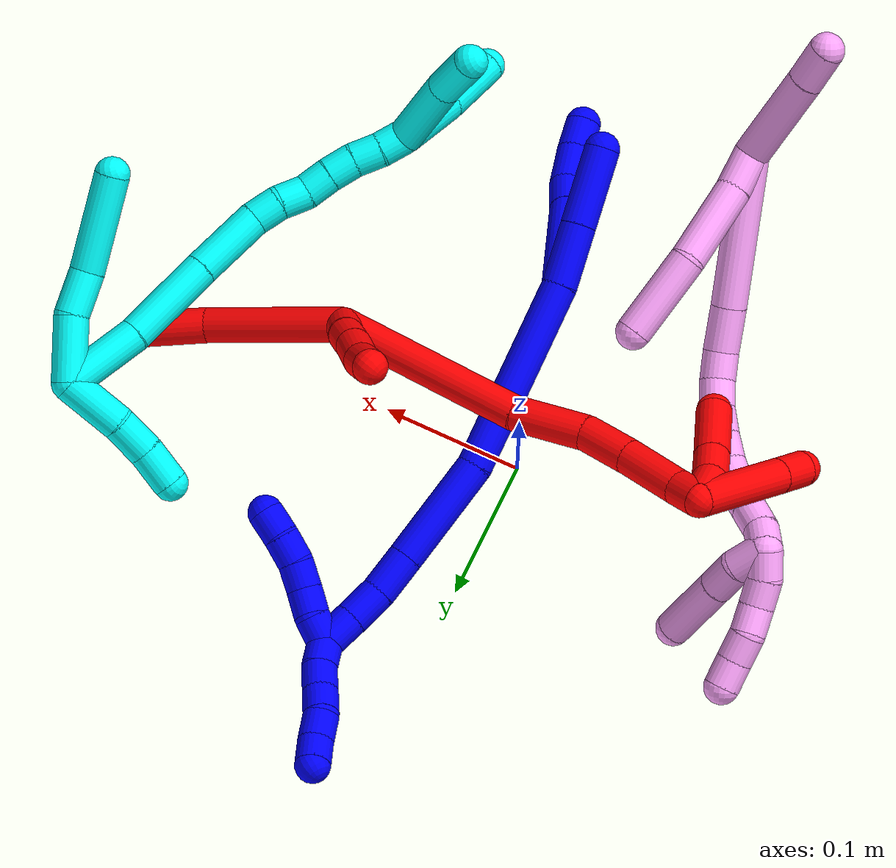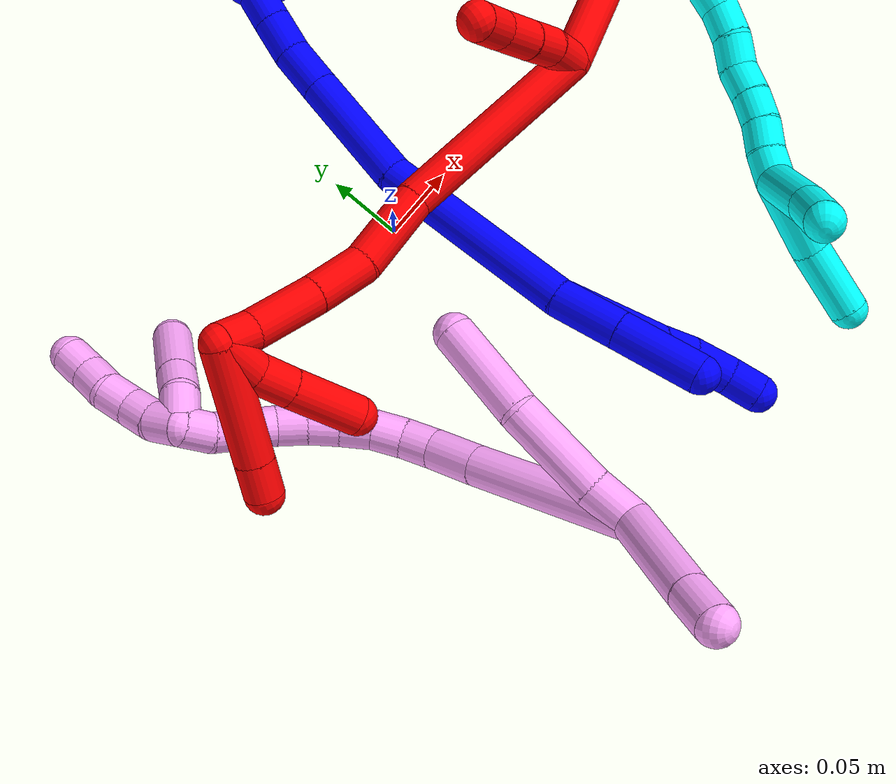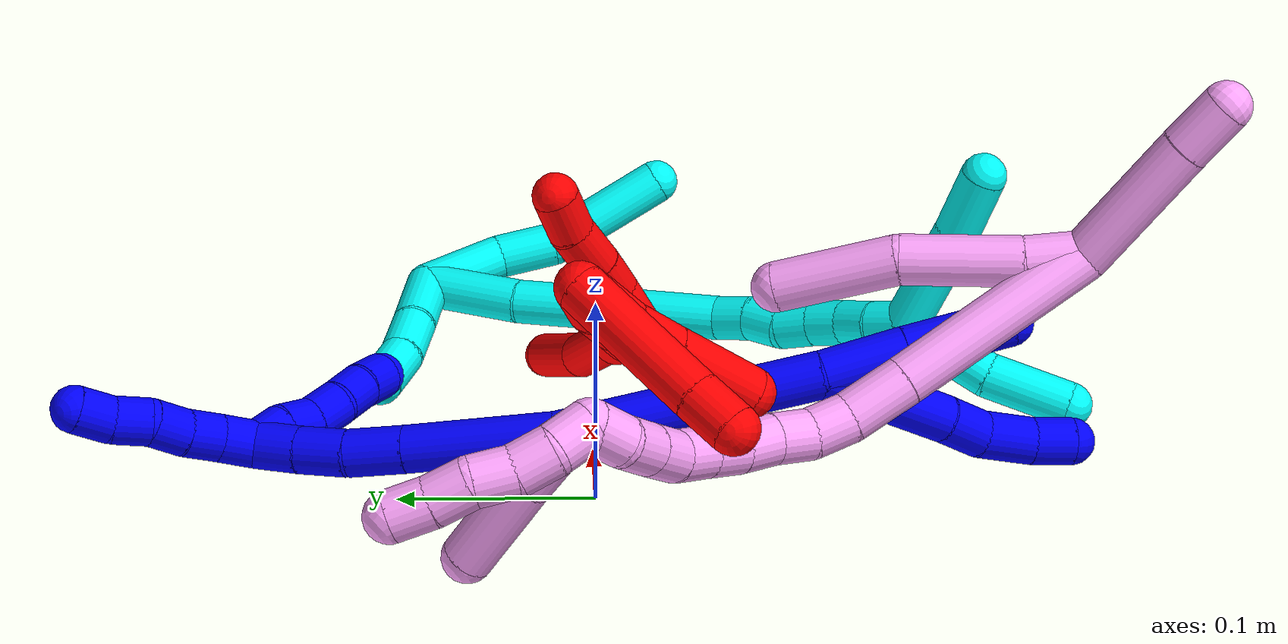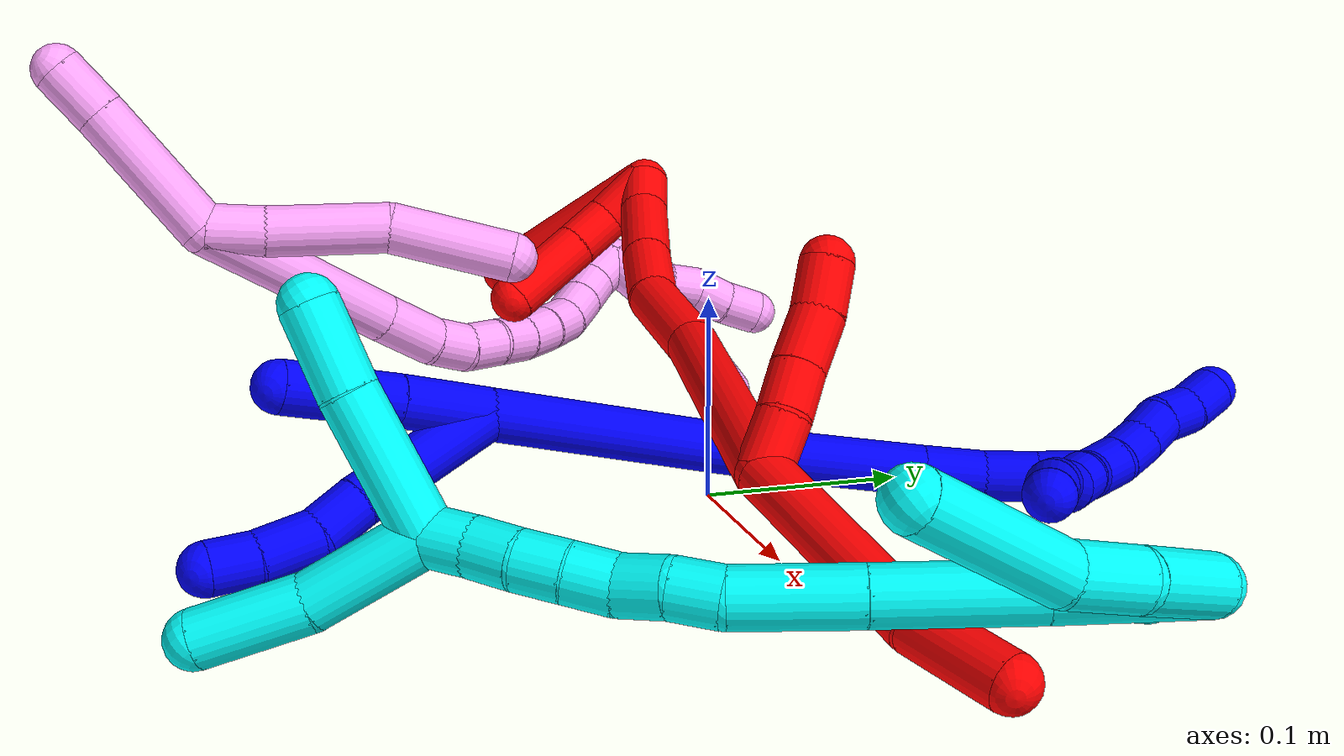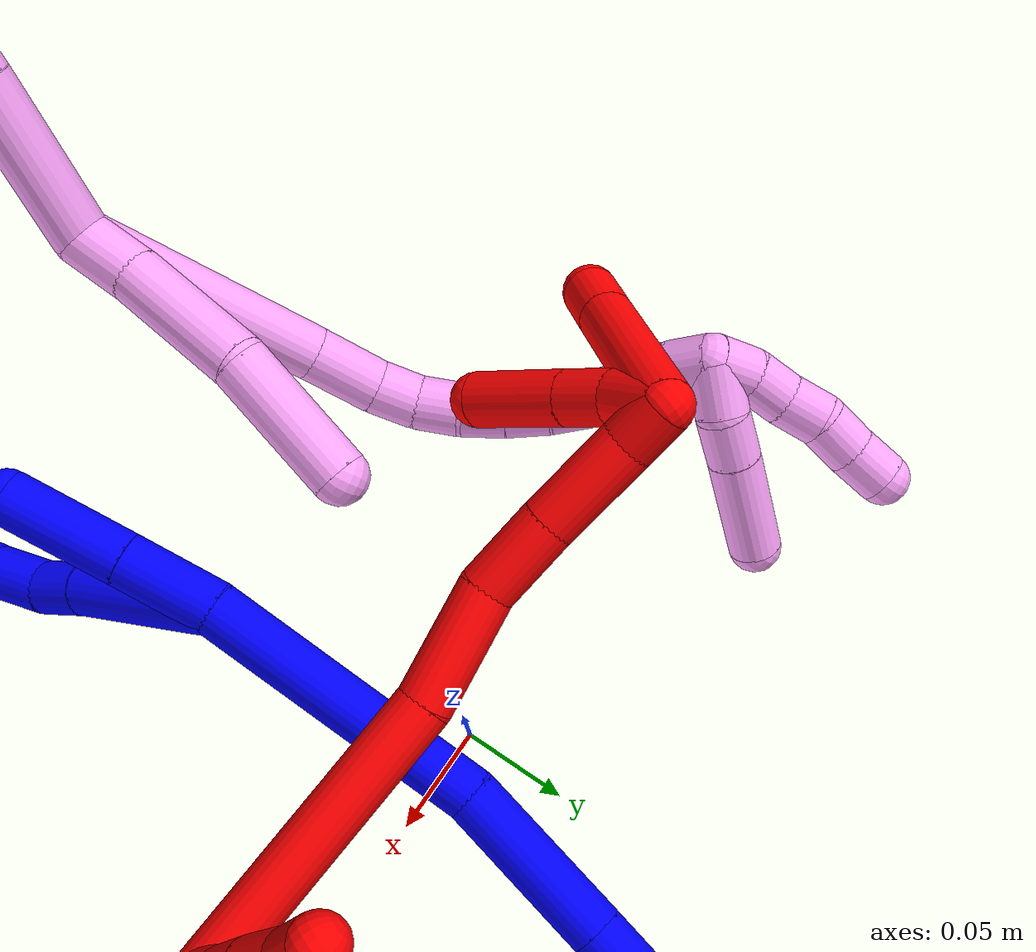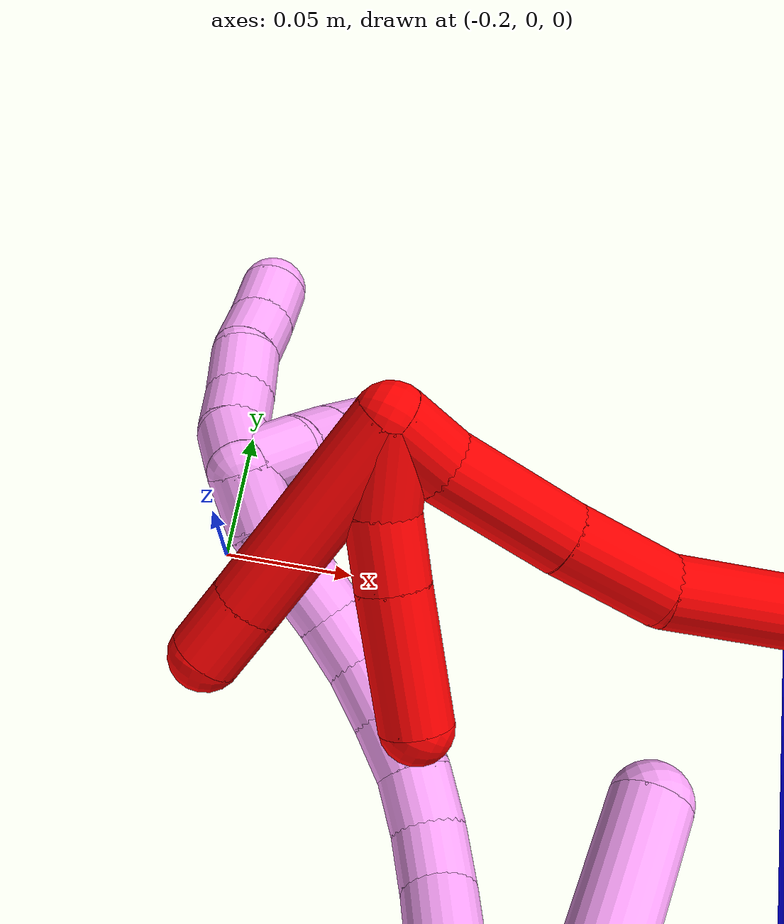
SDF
<sdf version="1.7">
 <world name="default">
  <plugin name="TubeGeneratorPlugin" filename="libtube_generator_plugin.so"/>
  <model name="photoneo_s_sensor">
   <static>1</static>
   <pose>0 0 2 1.57079 1.57079 3.14159</pose>
   <link name="link">
    <inertial><mass>0.1</mass></inertial>
    <sensor name="sensor" type="depth">
     <update_rate>30</update_rate>
     <camera>
      <horizontal_fov>1.22</horizontal_fov>
      <image><width>1920</width><height>1200</height><format>B8G8R8</format></image>
      <clip><near>0.1</near><far>4</far></clip>
      <depth_camera><output>points</output></depth_camera>
     </camera>
     <plugin name="camera_plugin" filename="libgazebo_ros_depth_camera.so">
      <baseline>0.2</baseline>
      <alwaysOn>1</alwaysOn>
      <updateRate>0.0</updateRate>
      <cameraName>camera_ir</cameraName>
      <imageTopicName>/camera/color/image_raw</imageTopicName>
      <cameraInfoTopicName>/camera/color/camera_info</cameraInfoTopicName>
      <depthImageTopicName>/camera/depth/image_raw</depthImageTopicName>
      <depthImageCameraInfoTopicName>/camera/depth/camera_info</depthImageCameraInfoTopicName>
      <pointCloudTopicName>/camera/depth/points</pointCloudTopicName>
      <frameName>fr_optical</frameName>
      <pointCloudCutoff>0.1</pointCloudCutoff>
      <pointCloudCutoffMax>2.0</pointCloudCutoffMax>
      <distortionK1>0</distortionK1>
      <distortionK2>0</distortionK2>
      <distortionK3>0</distortionK3>
      <distortionT1>0</distortionT1>
      <distortionT2>0</distortionT2>
      <CxPrime>0</CxPrime>
      <Cx>0</Cx>
      <Cy>0</Cy>
      <focalLength>0</focalLength>
      <hackBaseline>0</hackBaseline>
     </plugin>
    </sensor>
   </link>
  </model>
  <gravity>0 0 -9.8</gravity>
  <magnetic_field>6e-06 2.3e-05 -4.2e-05</magnetic_field>
  <atmosphere type="adiabatic"/>
  <physics name="default_physics" default="0" type="ode">
   <max_step_size>0.003</max_step_size>
   <real_time_factor>1</real_time_factor>
   <real_time_update_rate>1000</real_time_update_rate>
   <max_contacts>10000</max_contacts>
   <ode>
    <solver>
     <type>quick</type>
     <iters>100</iters>
     <sor>1.3</sor>
     <use_dynamic_moi_rescaling>0</use_dynamic_moi_rescaling>
    </solver>
    <constraints>
     <contact_max_correcting_vel>0</contact_max_correcting_vel>
     <contact_surface_layer>0.001</contact_surface_layer>
     <cfm>0</cfm>
     <erp>0.2</erp>
    </constraints>
   </ode>
  </physics>
  <scene><ambient>0.4 0.4 0.4 1</ambient><background>0.7 0.7 0.7 1</background><shadows>0</shadows></scene>
  <audio><device>default</device></audio>
  <spherical_coordinates>
   <surface_model>EARTH_WGS84</surface_model>
   <latitude_deg>0</latitude_deg>
   <longitude_deg>0</longitude_deg>
   <elevation>0</elevation>
   <heading_deg>0</heading_deg>
  </spherical_coordinates>
  <model name="bin">
   <static>1</static>
   <link name="bottom">
    <collision name="collision-bottom">
     <pose>0 0 -0.01 0 -0 0</pose>
     <geometry><box><size>0.8 0.6 0.02</size></box></geometry>
     <surface>
      <friction><ode><mu>100</mu><mu2>100</mu2></ode></friction>
      <contact><collide_bitmask>65535</collide_bitmask></contact>
     </surface>
    </collision>
   </link>
   <link name="west_wall">
    <collision name="collision-west_wall">
     <pose>-0.41 0 0.1 0 -0 0</pose>
     <geometry><box><size>0.02 0.6 0.2</size></box></geometry>
     <surface>
      <friction><ode><mu>100</mu><mu2>100</mu2></ode></friction>
      <contact><collide_bitmask>65535</collide_bitmask></contact>
     </surface>
    </collision>
   </link>
   <link name="east_wall">
    <collision name="collision-east_wall">
     <pose>0.41 0 0.1 0 -0 0</pose>
     <geometry><box><size>0.02 0.6 0.2</size></box></geometry>
     <surface>
      <friction><ode><mu>100</mu><mu2>100</mu2></ode></friction>
      <contact><collide_bitmask>65535</collide_bitmask></contact>
     </surface>
    </collision>
   </link>
   <link name="south_wall">
    <collision name="collision-south_wall">
     <pose>0 -0.31 0.1 0 -0 0</pose>
     <geometry><box><size>0.8 0.02 0.2</size></box></geometry>
     <surface>
      <friction><ode><mu>100</mu><mu2>100</mu2></ode></friction>
      <contact><collide_bitmask>65535</collide_bitmask></contact>
     </surface>
    </collision>
   </link>
   <link name="north_wall">
    <collision name="collision-north_wall">
     <pose>0 0.31 0.1 0 -0 0</pose>
     <geometry><box><size>0.8 0.02 0.2</size></box></geometry>
     <surface>
      <friction><ode><mu>100</mu><mu2>100</mu2></ode></friction>
      <contact><collide_bitmask>65535</collide_bitmask></contact>
     </surface>
    </collision>
   </link>
  </model>
  <model name="1">
   <static>0</static>
   <link name="1">
    <collision name="collision-cylinder-e_1_2_8">
     <pose>0.013427 -0.020258 0.02851 0.617774 0.366557 0.118159</pose>
     <geometry><cylinder><radius>0.0125</radius><length>0.074926</length></cylinder></geometry>
     <surface>
      <friction><ode><mu>1.16</mu><mu2>1.16</mu2><slip1>0</slip1><slip2>0</slip2></ode></friction>
      <contact><ode><kp>1e+06</kp><kd>1</kd><max_vel>0</max_vel><min_depth>0.001</min_depth></ode></contact>
     </surface>
    </collision>
    <visual name="visual-cylinder-e_1_2_8">
     <pose>0.013427 -0.020258 0.02851 0.617774 0.366557 0.118159</pose>
     <geometry><cylinder><radius>0.0125</radius><length>0.074926</length></cylinder></geometry>
     <material><ambient>0 0 1 1</ambient></material>
    </visual>
    <collision name="collision-cylinder-e_2_8_9">
     <pose>0.031787 -0.046164 0.066571 0.534077 0.418345 0.116016</pose>
     <geometry><cylinder><radius>0.0125</radius><length>0.024288</length></cylinder></geometry>
     <surface>
      <friction><ode><mu>1.16</mu><mu2>1.16</mu2><slip1>0</slip1><slip2>0</slip2></ode></friction>
      <contact><ode><kp>1e+06</kp><kd>1</kd><max_vel>0</max_vel><min_depth>0.001</min_depth></ode></contact>
     </surface>
    </collision>
    <visual name="visual-cylinder-e_2_8_9">
     <pose>0.031787 -0.046164 0.066571 0.534077 0.418345 0.116016</pose>
     <geometry><cylinder><radius>0.0125</radius><length>0.024288</length></cylinder></geometry>
     <material><ambient>0 0 1 1</ambient></material>
    </visual>
    <collision name="collision-cylinder-e_3_9_10">
     <pose>0.038983 -0.061125 0.086797 0.717321 0.158347 0.059467</pose>
     <geometry><cylinder><radius>0.0125</radius><length>0.028689</length></cylinder></geometry>
     <surface>
      <friction><ode><mu>1.16</mu><mu2>1.16</mu2><slip1>0</slip1><slip2>0</slip2></ode></friction>
      <contact><ode><kp>1e+06</kp><kd>1</kd><max_vel>0</max_vel><min_depth>0.001</min_depth></ode></contact>
     </surface>
    </collision>
    <visual name="visual-cylinder-e_3_9_10">
     <pose>0.038983 -0.061125 0.086797 0.717321 0.158347 0.059467</pose>
     <geometry><cylinder><radius>0.0125</radius><length>0.028689</length></cylinder></geometry>
     <material><ambient>0 0 1 1</ambient></material>
    </visual>
    <collision name="collision-cylinder-e_4_10_6">
     <pose>0.041461 -0.078334 0.105195 0.796494 0.0196 0.008246</pose>
     <geometry><cylinder><radius>0.0125</radius><length>0.022097</length></cylinder></geometry>
     <surface>
      <friction><ode><mu>1.16</mu><mu2>1.16</mu2><slip1>0</slip1><slip2>0</slip2></ode></friction>
      <contact><ode><kp>1e+06</kp><kd>1</kd><max_vel>0</max_vel><min_depth>0.001</min_depth></ode></contact>
     </surface>
    </collision>
    <visual name="visual-cylinder-e_4_10_6">
     <pose>0.041461 -0.078334 0.105195 0.796494 0.0196 0.008246</pose>
     <geometry><cylinder><radius>0.0125</radius><length>0.022097</length></cylinder></geometry>
     <material><ambient>0 0 1 1</ambient></material>
    </visual>
    <collision name="collision-cylinder-e_1_2_11">
     <pose>-0.006325 -0.015392 0.014365 0.81987 -0.291863 -0.127565</pose>
     <geometry><cylinder><radius>0.0125</radius><length>0.043967</length></cylinder></geometry>
     <surface>
      <friction><ode><mu>1.16</mu><mu2>1.16</mu2><slip1>0</slip1><slip2>0</slip2></ode></friction>
      <contact><ode><kp>1e+06</kp><kd>1</kd><max_vel>0</max_vel><min_depth>0.001</min_depth></ode></contact>
     </surface>
    </collision>
    <visual name="visual-cylinder-e_1_2_11">
     <pose>-0.006325 -0.015392 0.014365 0.81987 -0.291863 -0.127565</pose>
     <geometry><cylinder><radius>0.0125</radius><length>0.043967</length></cylinder></geometry>
     <material><ambient>0 0 1 1</ambient></material>
    </visual>
    <collision name="collision-cylinder-e_2_11_5">
     <pose>-0.019967 -0.050532 0.047207 0.818656 -0.264211 -0.115167</pose>
     <geometry><cylinder><radius>0.0125</radius><length>0.056033</length></cylinder></geometry>
     <surface>
      <friction><ode><mu>1.16</mu><mu2>1.16</mu2><slip1>0</slip1><slip2>0</slip2></ode></friction>
      <contact><ode><kp>1e+06</kp><kd>1</kd><max_vel>0</max_vel><min_depth>0.001</min_depth></ode></contact>
     </surface>
    </collision>
    <visual name="visual-cylinder-e_2_11_5">
     <pose>-0.019967 -0.050532 0.047207 0.818656 -0.264211 -0.115167</pose>
     <geometry><cylinder><radius>0.0125</radius><length>0.056033</length></cylinder></geometry>
     <material><ambient>0 0 1 1</ambient></material>
    </visual>
    <collision name="collision-cylinder-e_1_2_12">
     <pose>0.018118 0.054744 -0.038272 -2.18092 0.264875 -0.500629</pose>
     <geometry><cylinder><radius>0.0125</radius><length>0.138419</length></cylinder></geometry>
     <surface>
      <friction><ode><mu>1.16</mu><mu2>1.16</mu2><slip1>0</slip1><slip2>0</slip2></ode></friction>
      <contact><ode><kp>1e+06</kp><kd>1</kd><max_vel>0</max_vel><min_depth>0.001</min_depth></ode></contact>
     </surface>
    </collision>
    <visual name="visual-cylinder-e_1_2_12">
     <pose>0.018118 0.054744 -0.038272 -2.18092 0.264875 -0.500629</pose>
     <geometry><cylinder><radius>0.0125</radius><length>0.138419</length></cylinder></geometry>
     <material><ambient>0 0 1 1</ambient></material>
    </visual>
    <collision name="collision-cylinder-e_2_12_13">
     <pose>0.043162 0.145424 -0.092051 -1.97817 0.175128 -0.265419</pose>
     <geometry><cylinder><radius>0.0125</radius><length>0.079492</length></cylinder></geometry>
     <surface>
      <friction><ode><mu>1.16</mu><mu2>1.16</mu2><slip1>0</slip1><slip2>0</slip2></ode></friction>
      <contact><ode><kp>1e+06</kp><kd>1</kd><max_vel>0</max_vel><min_depth>0.001</min_depth></ode></contact>
     </surface>
    </collision>
    <visual name="visual-cylinder-e_2_12_13">
     <pose>0.043162 0.145424 -0.092051 -1.97817 0.175128 -0.265419</pose>
     <geometry><cylinder><radius>0.0125</radius><length>0.079492</length></cylinder></geometry>
     <material><ambient>0 0 1 1</ambient></material>
    </visual>
    <collision name="collision-cylinder-e_3_13_14">
     <pose>0.052492 0.195379 -0.11349 -1.97117 0.156712 -0.23588</pose>
     <geometry><cylinder><radius>0.0125</radius><length>0.030825</length></cylinder></geometry>
     <surface>
      <friction><ode><mu>1.16</mu><mu2>1.16</mu2><slip1>0</slip1><slip2>0</slip2></ode></friction>
      <contact><ode><kp>1e+06</kp><kd>1</kd><max_vel>0</max_vel><min_depth>0.001</min_depth></ode></contact>
     </surface>
    </collision>
    <visual name="visual-cylinder-e_3_13_14">
     <pose>0.052492 0.195379 -0.11349 -1.97117 0.156712 -0.23588</pose>
     <geometry><cylinder><radius>0.0125</radius><length>0.030825</length></cylinder></geometry>
     <material><ambient>0 0 1 1</ambient></material>
    </visual>
    <collision name="collision-cylinder-e_4_14_15">
     <pose>0.055508 0.222104 -0.12312 -1.85389 0.046093 -0.061405</pose>
     <geometry><cylinder><radius>0.0125</radius><length>0.026492</length></cylinder></geometry>
     <surface>
      <friction><ode><mu>1.16</mu><mu2>1.16</mu2><slip1>0</slip1><slip2>0</slip2></ode></friction>
      <contact><ode><kp>1e+06</kp><kd>1</kd><max_vel>0</max_vel><min_depth>0.001</min_depth></ode></contact>
     </surface>
    </collision>
    <visual name="visual-cylinder-e_4_14_15">
     <pose>0.055508 0.222104 -0.12312 -1.85389 0.046093 -0.061405</pose>
     <geometry><cylinder><radius>0.0125</radius><length>0.026492</length></cylinder></geometry>
     <material><ambient>0 0 1 1</ambient></material>
    </visual>
    <collision name="collision-cylinder-e_5_15_1">
     <pose>0.056154 0.24675 -0.130105 -1.83959 0.002898 -0.003805</pose>
     <geometry><cylinder><radius>0.0125</radius><length>0.024772</length></cylinder></geometry>
     <surface>
      <friction><ode><mu>1.16</mu><mu2>1.16</mu2><slip1>0</slip1><slip2>0</slip2></ode></friction>
      <contact><ode><kp>1e+06</kp><kd>1</kd><max_vel>0</max_vel><min_depth>0.001</min_depth></ode></contact>
     </surface>
    </collision>
    <visual name="visual-cylinder-e_5_15_1">
     <pose>0.056154 0.24675 -0.130105 -1.83959 0.002898 -0.003805</pose>
     <geometry><cylinder><radius>0.0125</radius><length>0.024772</length></cylinder></geometry>
     <material><ambient>0 0 1 1</ambient></material>
    </visual>
    <collision name="collision-cylinder-e_1_1_16">
     <pose>0.05353 0.258477 -0.123757 0.022206 -0.269211 -0.003007</pose>
     <geometry><cylinder><radius>0.0125</radius><length>0.02</length></cylinder></geometry>
     <surface>
      <friction><ode><mu>1.16</mu><mu2>1.16</mu2><slip1>0</slip1><slip2>0</slip2></ode></friction>
      <contact><ode><kp>1e+06</kp><kd>1</kd><max_vel>0</max_vel><min_depth>0.001</min_depth></ode></contact>
     </surface>
    </collision>
    <visual name="visual-cylinder-e_1_1_16">
     <pose>0.05353 0.258477 -0.123757 0.022206 -0.269211 -0.003007</pose>
     <geometry><cylinder><radius>0.0125</radius><length>0.02</length></cylinder></geometry>
     <material><ambient>0 0 1 1</ambient></material>
    </visual>
    <collision name="collision-cylinder-e_2_16_17">
     <pose>0.050448 0.255948 -0.1044 0.233812 -0.042263 -0.004964</pose>
     <geometry><cylinder><radius>0.0125</radius><length>0.02</length></cylinder></geometry>
     <surface>
      <friction><ode><mu>1.16</mu><mu2>1.16</mu2><slip1>0</slip1><slip2>0</slip2></ode></friction>
      <contact><ode><kp>1e+06</kp><kd>1</kd><max_vel>0</max_vel><min_depth>0.001</min_depth></ode></contact>
     </surface>
    </collision>
    <visual name="visual-cylinder-e_2_16_17">
     <pose>0.050448 0.255948 -0.1044 0.233812 -0.042263 -0.004964</pose>
     <geometry><cylinder><radius>0.0125</radius><length>0.02</length></cylinder></geometry>
     <material><ambient>0 0 1 1</ambient></material>
    </visual>
    <collision name="collision-cylinder-e_3_17_18">
     <pose>0.046568 0.252048 -0.085433 0.169829 -0.353027 -0.030363</pose>
     <geometry><cylinder><radius>0.0125</radius><length>0.02</length></cylinder></geometry>
     <surface>
      <friction><ode><mu>1.16</mu><mu2>1.16</mu2><slip1>0</slip1><slip2>0</slip2></ode></friction>
      <contact><ode><kp>1e+06</kp><kd>1</kd><max_vel>0</max_vel><min_depth>0.001</min_depth></ode></contact>
     </surface>
    </collision>
    <visual name="visual-cylinder-e_3_17_18">
     <pose>0.046568 0.252048 -0.085433 0.169829 -0.353027 -0.030363</pose>
     <geometry><cylinder><radius>0.0125</radius><length>0.02</length></cylinder></geometry>
     <material><ambient>0 0 1 1</ambient></material>
    </visual>
    <collision name="collision-cylinder-e_4_18_19">
     <pose>0.040483 0.25076 -0.066541 -0.030887 -0.265924 0.004131</pose>
     <geometry><cylinder><radius>0.0125</radius><length>0.02</length></cylinder></geometry>
     <surface>
      <friction><ode><mu>1.16</mu><mu2>1.16</mu2><slip1>0</slip1><slip2>0</slip2></ode></friction>
      <contact><ode><kp>1e+06</kp><kd>1</kd><max_vel>0</max_vel><min_depth>0.001</min_depth></ode></contact>
     </surface>
    </collision>
    <visual name="visual-cylinder-e_4_18_19">
     <pose>0.040483 0.25076 -0.066541 -0.030887 -0.265924 0.004131</pose>
     <geometry><cylinder><radius>0.0125</radius><length>0.02</length></cylinder></geometry>
     <material><ambient>0 0 1 1</ambient></material>
    </visual>
    <collision name="collision-cylinder-e_5_19_4">
     <pose>0.036807 0.251752 -0.046976 -0.069831 -0.104954 0.003669</pose>
     <geometry><cylinder><radius>0.0125</radius><length>0.02</length></cylinder></geometry>
     <surface>
      <friction><ode><mu>1.16</mu><mu2>1.16</mu2><slip1>0</slip1><slip2>0</slip2></ode></friction>
      <contact><ode><kp>1e+06</kp><kd>1</kd><max_vel>0</max_vel><min_depth>0.001</min_depth></ode></contact>
     </surface>
    </collision>
    <visual name="visual-cylinder-e_5_19_4">
     <pose>0.036807 0.251752 -0.046976 -0.069831 -0.104954 0.003669</pose>
     <geometry><cylinder><radius>0.0125</radius><length>0.02</length></cylinder></geometry>
     <material><ambient>0 0 1 1</ambient></material>
    </visual>
    <collision name="collision-cylinder-e_1_1_20">
     <pose>0.054108 0.265082 -0.140799 -2.4296 -0.209726 0.55167</pose>
     <geometry><cylinder><radius>0.0125</radius><length>0.02</length></cylinder></geometry>
     <surface>
      <friction><ode><mu>1.16</mu><mu2>1.16</mu2><slip1>0</slip1><slip2>0</slip2></ode></friction>
      <contact><ode><kp>1e+06</kp><kd>1</kd><max_vel>0</max_vel><min_depth>0.001</min_depth></ode></contact>
     </surface>
    </collision>
    <visual name="visual-cylinder-e_1_1_20">
     <pose>0.054108 0.265082 -0.140799 -2.4296 -0.209726 0.55167</pose>
     <geometry><cylinder><radius>0.0125</radius><length>0.02</length></cylinder></geometry>
     <material><ambient>0 0 1 1</ambient></material>
    </visual>
    <collision name="collision-cylinder-e_2_20_21">
     <pose>0.049725 0.275934 -0.156852 -2.66522 -0.232263 0.895816</pose>
     <geometry><cylinder><radius>0.0125</radius><length>0.02</length></cylinder></geometry>
     <surface>
      <friction><ode><mu>1.16</mu><mu2>1.16</mu2><slip1>0</slip1><slip2>0</slip2></ode></friction>
      <contact><ode><kp>1e+06</kp><kd>1</kd><max_vel>0</max_vel><min_depth>0.001</min_depth></ode></contact>
     </surface>
    </collision>
    <visual name="visual-cylinder-e_2_20_21">
     <pose>0.049725 0.275934 -0.156852 -2.66522 -0.232263 0.895816</pose>
     <geometry><cylinder><radius>0.0125</radius><length>0.02</length></cylinder></geometry>
     <material><ambient>0 0 1 1</ambient></material>
    </visual>
    <collision name="collision-cylinder-e_3_21_22">
     <pose>0.043798 0.284684 -0.173776 -2.66361 -0.370871 1.31226</pose>
     <geometry><cylinder><radius>0.0125</radius><length>0.02</length></cylinder></geometry>
     <surface>
      <friction><ode><mu>1.16</mu><mu2>1.16</mu2><slip1>0</slip1><slip2>0</slip2></ode></friction>
      <contact><ode><kp>1e+06</kp><kd>1</kd><max_vel>0</max_vel><min_depth>0.001</min_depth></ode></contact>
     </surface>
    </collision>
    <visual name="visual-cylinder-e_3_21_22">
     <pose>0.043798 0.284684 -0.173776 -2.66361 -0.370871 1.31226</pose>
     <geometry><cylinder><radius>0.0125</radius><length>0.02</length></cylinder></geometry>
     <material><ambient>0 0 1 1</ambient></material>
    </visual>
    <collision name="collision-cylinder-e_4_22_23">
     <pose>0.039248 0.295344 -0.189701 -2.44702 -0.092798 0.25517</pose>
     <geometry><cylinder><radius>0.0125</radius><length>0.02</length></cylinder></geometry>
     <surface>
      <friction><ode><mu>1.16</mu><mu2>1.16</mu2><slip1>0</slip1><slip2>0</slip2></ode></friction>
      <contact><ode><kp>1e+06</kp><kd>1</kd><max_vel>0</max_vel><min_depth>0.001</min_depth></ode></contact>
     </surface>
    </collision>
    <visual name="visual-cylinder-e_4_22_23">
     <pose>0.039248 0.295344 -0.189701 -2.44702 -0.092798 0.25517</pose>
     <geometry><cylinder><radius>0.0125</radius><length>0.02</length></cylinder></geometry>
     <material><ambient>0 0 1 1</ambient></material>
    </visual>
    <collision name="collision-cylinder-e_5_23_3">
     <pose>0.035046 0.307168 -0.205069 -2.52661 -0.333675 0.975179</pose>
     <geometry><cylinder><radius>0.0125</radius><length>0.02</length></cylinder></geometry>
     <surface>
      <friction><ode><mu>1.16</mu><mu2>1.16</mu2><slip1>0</slip1><slip2>0</slip2></ode></friction>
      <contact><ode><kp>1e+06</kp><kd>1</kd><max_vel>0</max_vel><min_depth>0.001</min_depth></ode></contact>
     </surface>
    </collision>
    <visual name="visual-cylinder-e_5_23_3">
     <pose>0.035046 0.307168 -0.205069 -2.52661 -0.333675 0.975179</pose>
     <geometry><cylinder><radius>0.0125</radius><length>0.02</length></cylinder></geometry>
     <material><ambient>0 0 1 1</ambient></material>
    </visual>
    <collision name="collision-sphere-3">
     <pose>0.031771 0.312619 -0.212786 0 -0 0</pose>
     <geometry><sphere><radius>0.0125</radius></sphere></geometry>
     <surface>
      <friction><ode><mu>1.16</mu><mu2>1.16</mu2><slip1>0</slip1><slip2>0</slip2></ode></friction>
      <contact><ode><kp>1e+06</kp><kd>1</kd><max_vel>0</max_vel><min_depth>0.001</min_depth></ode></contact>
     </surface>
    </collision>
    <visual name="visual-sphere-3">
     <pose>0.031771 0.312619 -0.212786 0 -0 0</pose>
     <geometry><sphere><radius>0.0125</radius></sphere></geometry>
     <material><ambient>0 0 1 1</ambient></material>
    </visual>
    <collision name="collision-sphere-23">
     <pose>0.038321 0.301717 -0.197352 0 -0 0</pose>
     <geometry><sphere><radius>0.0125</radius></sphere></geometry>
     <surface>
      <friction><ode><mu>1.16</mu><mu2>1.16</mu2><slip1>0</slip1><slip2>0</slip2></ode></friction>
      <contact><ode><kp>1e+06</kp><kd>1</kd><max_vel>0</max_vel><min_depth>0.001</min_depth></ode></contact>
     </surface>
    </collision>
    <visual name="visual-sphere-23">
     <pose>0.038321 0.301717 -0.197352 0 -0 0</pose>
     <geometry><sphere><radius>0.0125</radius></sphere></geometry>
     <material><ambient>0 0 1 1</ambient></material>
    </visual>
    <collision name="collision-sphere-22">
     <pose>0.040174 0.288971 -0.182051 0 -0 0</pose>
     <geometry><sphere><radius>0.0125</radius></sphere></geometry>
     <surface>
      <friction><ode><mu>1.16</mu><mu2>1.16</mu2><slip1>0</slip1><slip2>0</slip2></ode></friction>
      <contact><ode><kp>1e+06</kp><kd>1</kd><max_vel>0</max_vel><min_depth>0.001</min_depth></ode></contact>
     </surface>
    </collision>
    <visual name="visual-sphere-22">
     <pose>0.040174 0.288971 -0.182051 0 -0 0</pose>
     <geometry><sphere><radius>0.0125</radius></sphere></geometry>
     <material><ambient>0 0 1 1</ambient></material>
    </visual>
    <collision name="collision-sphere-21">
     <pose>0.047423 0.280397 -0.1655 0 -0 0</pose>
     <geometry><sphere><radius>0.0125</radius></sphere></geometry>
     <surface>
      <friction><ode><mu>1.16</mu><mu2>1.16</mu2><slip1>0</slip1><slip2>0</slip2></ode></friction>
      <contact><ode><kp>1e+06</kp><kd>1</kd><max_vel>0</max_vel><min_depth>0.001</min_depth></ode></contact>
     </surface>
    </collision>
    <visual name="visual-sphere-21">
     <pose>0.047423 0.280397 -0.1655 0 -0 0</pose>
     <geometry><sphere><radius>0.0125</radius></sphere></geometry>
     <material><ambient>0 0 1 1</ambient></material>
    </visual>
    <collision name="collision-sphere-20">
     <pose>0.052026 0.271472 -0.148204 0 -0 0</pose>
     <geometry><sphere><radius>0.0125</radius></sphere></geometry>
     <surface>
      <friction><ode><mu>1.16</mu><mu2>1.16</mu2><slip1>0</slip1><slip2>0</slip2></ode></friction>
      <contact><ode><kp>1e+06</kp><kd>1</kd><max_vel>0</max_vel><min_depth>0.001</min_depth></ode></contact>
     </surface>
    </collision>
    <visual name="visual-sphere-20">
     <pose>0.052026 0.271472 -0.148204 0 -0 0</pose>
     <geometry><sphere><radius>0.0125</radius></sphere></geometry>
     <material><ambient>0 0 1 1</ambient></material>
    </visual>
    <collision name="collision-sphere-4">
     <pose>0.03576 0.252445 -0.037055 0 -0 0</pose>
     <geometry><sphere><radius>0.0125</radius></sphere></geometry>
     <surface>
      <friction><ode><mu>1.16</mu><mu2>1.16</mu2><slip1>0</slip1><slip2>0</slip2></ode></friction>
      <contact><ode><kp>1e+06</kp><kd>1</kd><max_vel>0</max_vel><min_depth>0.001</min_depth></ode></contact>
     </surface>
    </collision>
    <visual name="visual-sphere-4">
     <pose>0.03576 0.252445 -0.037055 0 -0 0</pose>
     <geometry><sphere><radius>0.0125</radius></sphere></geometry>
     <material><ambient>0 0 1 1</ambient></material>
    </visual>
    <collision name="collision-sphere-11">
     <pose>-0.012651 -0.030783 0.028731 0 -0 0</pose>
     <geometry><sphere><radius>0.0125</radius></sphere></geometry>
     <surface>
      <friction><ode><mu>1.16</mu><mu2>1.16</mu2><slip1>0</slip1><slip2>0</slip2></ode></friction>
      <contact><ode><kp>1e+06</kp><kd>1</kd><max_vel>0</max_vel><min_depth>0.001</min_depth></ode></contact>
     </surface>
    </collision>
    <visual name="visual-sphere-11">
     <pose>-0.012651 -0.030783 0.028731 0 -0 0</pose>
     <geometry><sphere><radius>0.0125</radius></sphere></geometry>
     <material><ambient>0 0 1 1</ambient></material>
    </visual>
    <collision name="collision-sphere-6">
     <pose>0.041678 -0.086231 0.112919 0 -0 0</pose>
     <geometry><sphere><radius>0.0125</radius></sphere></geometry>
     <surface>
      <friction><ode><mu>1.16</mu><mu2>1.16</mu2><slip1>0</slip1><slip2>0</slip2></ode></friction>
      <contact><ode><kp>1e+06</kp><kd>1</kd><max_vel>0</max_vel><min_depth>0.001</min_depth></ode></contact>
     </surface>
    </collision>
    <visual name="visual-sphere-6">
     <pose>0.041678 -0.086231 0.112919 0 -0 0</pose>
     <geometry><sphere><radius>0.0125</radius></sphere></geometry>
     <material><ambient>0 0 1 1</ambient></material>
    </visual>
    <collision name="collision-sphere-10">
     <pose>0.041245 -0.070437 0.097471 0 -0 0</pose>
     <geometry><sphere><radius>0.0125</radius></sphere></geometry>
     <surface>
      <friction><ode><mu>1.16</mu><mu2>1.16</mu2><slip1>0</slip1><slip2>0</slip2></ode></friction>
      <contact><ode><kp>1e+06</kp><kd>1</kd><max_vel>0</max_vel><min_depth>0.001</min_depth></ode></contact>
     </surface>
    </collision>
    <visual name="visual-sphere-10">
     <pose>0.041245 -0.070437 0.097471 0 -0 0</pose>
     <geometry><sphere><radius>0.0125</radius></sphere></geometry>
     <material><ambient>0 0 1 1</ambient></material>
    </visual>
    <collision name="collision-sphere-9">
     <pose>0.036721 -0.051813 0.076123 0 -0 0</pose>
     <geometry><sphere><radius>0.0125</radius></sphere></geometry>
     <surface>
      <friction><ode><mu>1.16</mu><mu2>1.16</mu2><slip1>0</slip1><slip2>0</slip2></ode></friction>
      <contact><ode><kp>1e+06</kp><kd>1</kd><max_vel>0</max_vel><min_depth>0.001</min_depth></ode></contact>
     </surface>
    </collision>
    <visual name="visual-sphere-9">
     <pose>0.036721 -0.051813 0.076123 0 -0 0</pose>
     <geometry><sphere><radius>0.0125</radius></sphere></geometry>
     <material><ambient>0 0 1 1</ambient></material>
    </visual>
    <collision name="collision-sphere-2">
     <geometry><sphere><radius>0.0125</radius></sphere></geometry>
     <surface>
      <friction><ode><mu>1.16</mu><mu2>1.16</mu2><slip1>0</slip1><slip2>0</slip2></ode></friction>
      <contact><ode><kp>1e+06</kp><kd>1</kd><max_vel>0</max_vel><min_depth>0.001</min_depth></ode></contact>
     </surface>
    </collision>
    <visual name="visual-sphere-2">
     <geometry><sphere><radius>0.0125</radius></sphere></geometry>
     <material><ambient>0 0 1 1</ambient></material>
    </visual>
    <collision name="collision-sphere-19">
     <pose>0.037855 0.251058 -0.056897 0 -0 0</pose>
     <geometry><sphere><radius>0.0125</radius></sphere></geometry>
     <surface>
      <friction><ode><mu>1.16</mu><mu2>1.16</mu2><slip1>0</slip1><slip2>0</slip2></ode></friction>
      <contact><ode><kp>1e+06</kp><kd>1</kd><max_vel>0</max_vel><min_depth>0.001</min_depth></ode></contact>
     </surface>
    </collision>
    <visual name="visual-sphere-19">
     <pose>0.037855 0.251058 -0.056897 0 -0 0</pose>
     <geometry><sphere><radius>0.0125</radius></sphere></geometry>
     <material><ambient>0 0 1 1</ambient></material>
    </visual>
    <collision name="collision-sphere-8">
     <pose>0.026854 -0.040516 0.05702 0 -0 0</pose>
     <geometry><sphere><radius>0.0125</radius></sphere></geometry>
     <surface>
      <friction><ode><mu>1.16</mu><mu2>1.16</mu2><slip1>0</slip1><slip2>0</slip2></ode></friction>
      <contact><ode><kp>1e+06</kp><kd>1</kd><max_vel>0</max_vel><min_depth>0.001</min_depth></ode></contact>
     </surface>
    </collision>
    <visual name="visual-sphere-8">
     <pose>0.026854 -0.040516 0.05702 0 -0 0</pose>
     <geometry><sphere><radius>0.0125</radius></sphere></geometry>
     <material><ambient>0 0 1 1</ambient></material>
    </visual>
    <collision name="collision-sphere-5">
     <pose>-0.027284 -0.07028 0.065684 0 -0 0</pose>
     <geometry><sphere><radius>0.0125</radius></sphere></geometry>
     <surface>
      <friction><ode><mu>1.16</mu><mu2>1.16</mu2><slip1>0</slip1><slip2>0</slip2></ode></friction>
      <contact><ode><kp>1e+06</kp><kd>1</kd><max_vel>0</max_vel><min_depth>0.001</min_depth></ode></contact>
     </surface>
    </collision>
    <visual name="visual-sphere-5">
     <pose>-0.027284 -0.07028 0.065684 0 -0 0</pose>
     <geometry><sphere><radius>0.0125</radius></sphere></geometry>
     <material><ambient>0 0 1 1</ambient></material>
    </visual>
    <collision name="collision-sphere-12">
     <pose>0.036237 0.109489 -0.076544 0 -0 0</pose>
     <geometry><sphere><radius>0.0125</radius></sphere></geometry>
     <surface>
      <friction><ode><mu>1.16</mu><mu2>1.16</mu2><slip1>0</slip1><slip2>0</slip2></ode></friction>
      <contact><ode><kp>1e+06</kp><kd>1</kd><max_vel>0</max_vel><min_depth>0.001</min_depth></ode></contact>
     </surface>
    </collision>
    <visual name="visual-sphere-12">
     <pose>0.036237 0.109489 -0.076544 0 -0 0</pose>
     <geometry><sphere><radius>0.0125</radius></sphere></geometry>
     <material><ambient>0 0 1 1</ambient></material>
    </visual>
    <collision name="collision-sphere-13">
     <pose>0.050087 0.181359 -0.107557 0 -0 0</pose>
     <geometry><sphere><radius>0.0125</radius></sphere></geometry>
     <surface>
      <friction><ode><mu>1.16</mu><mu2>1.16</mu2><slip1>0</slip1><slip2>0</slip2></ode></friction>
      <contact><ode><kp>1e+06</kp><kd>1</kd><max_vel>0</max_vel><min_depth>0.001</min_depth></ode></contact>
     </surface>
    </collision>
    <visual name="visual-sphere-13">
     <pose>0.050087 0.181359 -0.107557 0 -0 0</pose>
     <geometry><sphere><radius>0.0125</radius></sphere></geometry>
     <material><ambient>0 0 1 1</ambient></material>
    </visual>
    <collision name="collision-sphere-14">
     <pose>0.054898 0.209399 -0.119424 0 -0 0</pose>
     <geometry><sphere><radius>0.0125</radius></sphere></geometry>
     <surface>
      <friction><ode><mu>1.16</mu><mu2>1.16</mu2><slip1>0</slip1><slip2>0</slip2></ode></friction>
      <contact><ode><kp>1e+06</kp><kd>1</kd><max_vel>0</max_vel><min_depth>0.001</min_depth></ode></contact>
     </surface>
    </collision>
    <visual name="visual-sphere-14">
     <pose>0.054898 0.209399 -0.119424 0 -0 0</pose>
     <geometry><sphere><radius>0.0125</radius></sphere></geometry>
     <material><ambient>0 0 1 1</ambient></material>
    </visual>
    <collision name="collision-sphere-15">
     <pose>0.056118 0.234809 -0.126816 0 -0 0</pose>
     <geometry><sphere><radius>0.0125</radius></sphere></geometry>
     <surface>
      <friction><ode><mu>1.16</mu><mu2>1.16</mu2><slip1>0</slip1><slip2>0</slip2></ode></friction>
      <contact><ode><kp>1e+06</kp><kd>1</kd><max_vel>0</max_vel><min_depth>0.001</min_depth></ode></contact>
     </surface>
    </collision>
    <visual name="visual-sphere-15">
     <pose>0.056118 0.234809 -0.126816 0 -0 0</pose>
     <geometry><sphere><radius>0.0125</radius></sphere></geometry>
     <material><ambient>0 0 1 1</ambient></material>
    </visual>
    <collision name="collision-sphere-1">
     <pose>0.05619 0.258691 -0.133395 0 -0 0</pose>
     <geometry><sphere><radius>0.0125</radius></sphere></geometry>
     <surface>
      <friction><ode><mu>1.16</mu><mu2>1.16</mu2><slip1>0</slip1><slip2>0</slip2></ode></friction>
      <contact><ode><kp>1e+06</kp><kd>1</kd><max_vel>0</max_vel><min_depth>0.001</min_depth></ode></contact>
     </surface>
    </collision>
    <visual name="visual-sphere-1">
     <pose>0.05619 0.258691 -0.133395 0 -0 0</pose>
     <geometry><sphere><radius>0.0125</radius></sphere></geometry>
     <material><ambient>0 0 1 1</ambient></material>
    </visual>
    <collision name="collision-sphere-18">
     <pose>0.043111 0.250462 -0.076185 0 -0 0</pose>
     <geometry><sphere><radius>0.0125</radius></sphere></geometry>
     <surface>
      <friction><ode><mu>1.16</mu><mu2>1.16</mu2><slip1>0</slip1><slip2>0</slip2></ode></friction>
      <contact><ode><kp>1e+06</kp><kd>1</kd><max_vel>0</max_vel><min_depth>0.001</min_depth></ode></contact>
     </surface>
    </collision>
    <visual name="visual-sphere-18">
     <pose>0.043111 0.250462 -0.076185 0 -0 0</pose>
     <geometry><sphere><radius>0.0125</radius></sphere></geometry>
     <material><ambient>0 0 1 1</ambient></material>
    </visual>
    <collision name="collision-sphere-16">
     <pose>0.050871 0.258263 -0.11412 0 -0 0</pose>
     <geometry><sphere><radius>0.0125</radius></sphere></geometry>
     <surface>
      <friction><ode><mu>1.16</mu><mu2>1.16</mu2><slip1>0</slip1><slip2>0</slip2></ode></friction>
      <contact><ode><kp>1e+06</kp><kd>1</kd><max_vel>0</max_vel><min_depth>0.001</min_depth></ode></contact>
     </surface>
    </collision>
    <visual name="visual-sphere-16">
     <pose>0.050871 0.258263 -0.11412 0 -0 0</pose>
     <geometry><sphere><radius>0.0125</radius></sphere></geometry>
     <material><ambient>0 0 1 1</ambient></material>
    </visual>
    <collision name="collision-sphere-17">
     <pose>0.050026 0.253634 -0.094681 0 -0 0</pose>
     <geometry><sphere><radius>0.0125</radius></sphere></geometry>
     <surface>
      <friction><ode><mu>1.16</mu><mu2>1.16</mu2><slip1>0</slip1><slip2>0</slip2></ode></friction>
      <contact><ode><kp>1e+06</kp><kd>1</kd><max_vel>0</max_vel><min_depth>0.001</min_depth></ode></contact>
     </surface>
    </collision>
    <visual name="visual-sphere-17">
     <pose>0.050026 0.253634 -0.094681 0 -0 0</pose>
     <geometry><sphere><radius>0.0125</radius></sphere></geometry>
     <material><ambient>0 0 1 1</ambient></material>
    </visual>
    <inertial>
     <pose>0.029106 0.108625 -0.048826 0 -0 0</pose>
     <mass>0.75</mass>
     <inertia>
      <ixx>0.000212</ixx>
      <ixy>0</ixy>
      <ixz>0</ixz>
      <iyy>-0.000149</iyy>
      <iyz>0</iyz>
      <izz>-0.000256</izz>
     </inertia>
    </inertial>
   </link>
   <pose>0.022886 -0.115321 0.057732 1.85784 1.53075 1.24369</pose>
  </model>
  <model name="2">
   <static>0</static>
   <link name="2">
    <collision name="collision-cylinder-e_1_2_8">
     <pose>0.030116 -0.006044 0.041065 0.146133 0.627665 0.047504</pose>
     <geometry><cylinder><radius>0.0125</radius><length>0.102564</length></cylinder></geometry>
     <surface>
      <friction><ode><mu>1.16</mu><mu2>1.16</mu2><slip1>0</slip1><slip2>0</slip2></ode></friction>
      <contact><ode><kp>1e+06</kp><kd>1</kd><max_vel>0</max_vel><min_depth>0.001</min_depth></ode></contact>
     </surface>
    </collision>
    <visual name="visual-cylinder-e_1_2_8">
     <pose>0.030116 -0.006044 0.041065 0.146133 0.627665 0.047504</pose>
     <geometry><cylinder><radius>0.0125</radius><length>0.102564</length></cylinder></geometry>
     <material><ambient>1 0 0 1</ambient></material>
    </visual>
    <collision name="collision-cylinder-e_2_8_6">
     <pose>0.076133 -0.010491 0.099656 -0.090908 0.734811 -0.035009</pose>
     <geometry><cylinder><radius>0.0125</radius><length>0.047436</length></cylinder></geometry>
     <surface>
      <friction><ode><mu>1.16</mu><mu2>1.16</mu2><slip1>0</slip1><slip2>0</slip2></ode></friction>
      <contact><ode><kp>1e+06</kp><kd>1</kd><max_vel>0</max_vel><min_depth>0.001</min_depth></ode></contact>
     </surface>
    </collision>
    <visual name="visual-cylinder-e_2_8_6">
     <pose>0.076133 -0.010491 0.099656 -0.090908 0.734811 -0.035009</pose>
     <geometry><cylinder><radius>0.0125</radius><length>0.047436</length></cylinder></geometry>
     <material><ambient>1 0 0 1</ambient></material>
    </visual>
    <collision name="collision-cylinder-e_1_2_9">
     <pose>0.001824 0.010641 -0.006868 -2.14394 0.143023 -0.261482</pose>
     <geometry><cylinder><radius>0.0125</radius><length>0.025591</length></cylinder></geometry>
     <surface>
      <friction><ode><mu>1.16</mu><mu2>1.16</mu2><slip1>0</slip1><slip2>0</slip2></ode></friction>
      <contact><ode><kp>1e+06</kp><kd>1</kd><max_vel>0</max_vel><min_depth>0.001</min_depth></ode></contact>
     </surface>
    </collision>
    <visual name="visual-cylinder-e_1_2_9">
     <pose>0.001824 0.010641 -0.006868 -2.14394 0.143023 -0.261482</pose>
     <geometry><cylinder><radius>0.0125</radius><length>0.025591</length></cylinder></geometry>
     <material><ambient>1 0 0 1</ambient></material>
    </visual>
    <collision name="collision-cylinder-e_2_9_10">
     <pose>0.004703 0.02954 -0.021303 -2.31261 0.09393 -0.212835</pose>
     <geometry><cylinder><radius>0.0125</radius><length>0.022502</length></cylinder></geometry>
     <surface>
      <friction><ode><mu>1.16</mu><mu2>1.16</mu2><slip1>0</slip1><slip2>0</slip2></ode></friction>
      <contact><ode><kp>1e+06</kp><kd>1</kd><max_vel>0</max_vel><min_depth>0.001</min_depth></ode></contact>
     </surface>
    </collision>
    <visual name="visual-cylinder-e_2_9_10">
     <pose>0.004703 0.02954 -0.021303 -2.31261 0.09393 -0.212835</pose>
     <geometry><cylinder><radius>0.0125</radius><length>0.022502</length></cylinder></geometry>
     <material><ambient>1 0 0 1</ambient></material>
    </visual>
    <collision name="collision-cylinder-e_3_10_11">
     <pose>0.007851 0.047647 -0.038044 -2.32067 0.154251 -0.351495</pose>
     <geometry><cylinder><radius>0.0125</radius><length>0.027242</length></cylinder></geometry>
     <surface>
      <friction><ode><mu>1.16</mu><mu2>1.16</mu2><slip1>0</slip1><slip2>0</slip2></ode></friction>
      <contact><ode><kp>1e+06</kp><kd>1</kd><max_vel>0</max_vel><min_depth>0.001</min_depth></ode></contact>
     </surface>
    </collision>
    <visual name="visual-cylinder-e_3_10_11">
     <pose>0.007851 0.047647 -0.038044 -2.32067 0.154251 -0.351495</pose>
     <geometry><cylinder><radius>0.0125</radius><length>0.027242</length></cylinder></geometry>
     <material><ambient>1 0 0 1</ambient></material>
    </visual>
    <collision name="collision-cylinder-e_4_11_5">
     <pose>0.009671 0.067311 -0.054681 -2.22092 -0.022083 0.044528</pose>
     <geometry><cylinder><radius>0.0125</radius><length>0.024666</length></cylinder></geometry>
     <surface>
      <friction><ode><mu>1.16</mu><mu2>1.16</mu2><slip1>0</slip1><slip2>0</slip2></ode></friction>
      <contact><ode><kp>1e+06</kp><kd>1</kd><max_vel>0</max_vel><min_depth>0.001</min_depth></ode></contact>
     </surface>
    </collision>
    <visual name="visual-cylinder-e_4_11_5">
     <pose>0.009671 0.067311 -0.054681 -2.22092 -0.022083 0.044528</pose>
     <geometry><cylinder><radius>0.0125</radius><length>0.024666</length></cylinder></geometry>
     <material><ambient>1 0 0 1</ambient></material>
    </visual>
    <collision name="collision-cylinder-e_1_2_12">
     <pose>-0.014073 -0.000421 -0.068647 3.13547 -0.202206 -3.08122</pose>
     <geometry><cylinder><radius>0.0125</radius><length>0.140152</length></cylinder></geometry>
     <surface>
      <friction><ode><mu>1.16</mu><mu2>1.16</mu2><slip1>0</slip1><slip2>0</slip2></ode></friction>
      <contact><ode><kp>1e+06</kp><kd>1</kd><max_vel>0</max_vel><min_depth>0.001</min_depth></ode></contact>
     </surface>
    </collision>
    <visual name="visual-cylinder-e_1_2_12">
     <pose>-0.014073 -0.000421 -0.068647 3.13547 -0.202206 -3.08122</pose>
     <geometry><cylinder><radius>0.0125</radius><length>0.140152</length></cylinder></geometry>
     <material><ambient>1 0 0 1</ambient></material>
    </visual>
    <collision name="collision-cylinder-e_2_12_13">
     <pose>-0.038419 3.4e-05 -0.161883 -3.106 -0.395491 2.96442</pose>
     <geometry><cylinder><radius>0.0125</radius><length>0.053327</length></cylinder></geometry>
     <surface>
      <friction><ode><mu>1.16</mu><mu2>1.16</mu2><slip1>0</slip1><slip2>0</slip2></ode></friction>
      <contact><ode><kp>1e+06</kp><kd>1</kd><max_vel>0</max_vel><min_depth>0.001</min_depth></ode></contact>
     </surface>
    </collision>
    <visual name="visual-cylinder-e_2_12_13">
     <pose>-0.038419 3.4e-05 -0.161883 -3.106 -0.395491 2.96442</pose>
     <geometry><cylinder><radius>0.0125</radius><length>0.053327</length></cylinder></geometry>
     <material><ambient>1 0 0 1</ambient></material>
    </visual>
    <collision name="collision-cylinder-e_3_13_14">
     <pose>-0.051564 0.004932 -0.204805 -2.92563 -0.151852 1.22381</pose>
     <geometry><cylinder><radius>0.0125</radius><length>0.037973</length></cylinder></geometry>
     <surface>
      <friction><ode><mu>1.16</mu><mu2>1.16</mu2><slip1>0</slip1><slip2>0</slip2></ode></friction>
      <contact><ode><kp>1e+06</kp><kd>1</kd><max_vel>0</max_vel><min_depth>0.001</min_depth></ode></contact>
     </surface>
    </collision>
    <visual name="visual-cylinder-e_3_13_14">
     <pose>-0.051564 0.004932 -0.204805 -2.92563 -0.151852 1.22381</pose>
     <geometry><cylinder><radius>0.0125</radius><length>0.037973</length></cylinder></geometry>
     <material><ambient>1 0 0 1</ambient></material>
    </visual>
    <collision name="collision-cylinder-e_4_14_15">
     <pose>-0.056957 0.014633 -0.245239 -2.89005 -0.110054 0.821702</pose>
     <geometry><cylinder><radius>0.0125</radius><length>0.045917</length></cylinder></geometry>
     <surface>
      <friction><ode><mu>1.16</mu><mu2>1.16</mu2><slip1>0</slip1><slip2>0</slip2></ode></friction>
      <contact><ode><kp>1e+06</kp><kd>1</kd><max_vel>0</max_vel><min_depth>0.001</min_depth></ode></contact>
     </surface>
    </collision>
    <visual name="visual-cylinder-e_4_14_15">
     <pose>-0.056957 0.014633 -0.245239 -2.89005 -0.110054 0.821702</pose>
     <geometry><cylinder><radius>0.0125</radius><length>0.045917</length></cylinder></geometry>
     <material><ambient>1 0 0 1</ambient></material>
    </visual>
    <collision name="collision-cylinder-e_5_15_1">
     <pose>-0.060775 0.025696 -0.277209 -2.6422 -0.114754 0.44308</pose>
     <geometry><cylinder><radius>0.0125</radius><length>0.022631</length></cylinder></geometry>
     <surface>
      <friction><ode><mu>1.16</mu><mu2>1.16</mu2><slip1>0</slip1><slip2>0</slip2></ode></friction>
      <contact><ode><kp>1e+06</kp><kd>1</kd><max_vel>0</max_vel><min_depth>0.001</min_depth></ode></contact>
     </surface>
    </collision>
    <visual name="visual-cylinder-e_5_15_1">
     <pose>-0.060775 0.025696 -0.277209 -2.6422 -0.114754 0.44308</pose>
     <geometry><cylinder><radius>0.0125</radius><length>0.022631</length></cylinder></geometry>
     <material><ambient>1 0 0 1</ambient></material>
    </visual>
    <collision name="collision-cylinder-e_1_1_16">
     <pose>-0.085196 0.001566 -0.294651 1.82201 -0.649211 -0.818557</pose>
     <geometry><cylinder><radius>0.0125</radius><length>0.076504</length></cylinder></geometry>
     <surface>
      <friction><ode><mu>1.16</mu><mu2>1.16</mu2><slip1>0</slip1><slip2>0</slip2></ode></friction>
      <contact><ode><kp>1e+06</kp><kd>1</kd><max_vel>0</max_vel><min_depth>0.001</min_depth></ode></contact>
     </surface>
    </collision>
    <visual name="visual-cylinder-e_1_1_16">
     <pose>-0.085196 0.001566 -0.294651 1.82201 -0.649211 -0.818557</pose>
     <geometry><cylinder><radius>0.0125</radius><length>0.076504</length></cylinder></geometry>
     <material><ambient>1 0 0 1</ambient></material>
    </visual>
    <collision name="collision-cylinder-e_2_16_4">
     <pose>-0.115651 -0.036809 -0.304624 1.83517 -0.673747 -0.858378</pose>
     <geometry><cylinder><radius>0.0125</radius><length>0.023496</length></cylinder></geometry>
     <surface>
      <friction><ode><mu>1.16</mu><mu2>1.16</mu2><slip1>0</slip1><slip2>0</slip2></ode></friction>
      <contact><ode><kp>1e+06</kp><kd>1</kd><max_vel>0</max_vel><min_depth>0.001</min_depth></ode></contact>
     </surface>
    </collision>
    <visual name="visual-cylinder-e_2_16_4">
     <pose>-0.115651 -0.036809 -0.304624 1.83517 -0.673747 -0.858378</pose>
     <geometry><cylinder><radius>0.0125</radius><length>0.023496</length></cylinder></geometry>
     <material><ambient>1 0 0 1</ambient></material>
    </visual>
    <collision name="collision-cylinder-e_1_1_17">
     <pose>-0.069707 0.019734 -0.282135 1.16 -0.552895 -0.367565</pose>
     <geometry><cylinder><radius>0.0125</radius><length>0.029084</length></cylinder></geometry>
     <surface>
      <friction><ode><mu>1.16</mu><mu2>1.16</mu2><slip1>0</slip1><slip2>0</slip2></ode></friction>
      <contact><ode><kp>1e+06</kp><kd>1</kd><max_vel>0</max_vel><min_depth>0.001</min_depth></ode></contact>
     </surface>
    </collision>
    <visual name="visual-cylinder-e_1_1_17">
     <pose>-0.069707 0.019734 -0.282135 1.16 -0.552895 -0.367565</pose>
     <geometry><cylinder><radius>0.0125</radius><length>0.029084</length></cylinder></geometry>
     <material><ambient>1 0 0 1</ambient></material>
    </visual>
    <collision name="collision-cylinder-e_2_17_18">
     <pose>-0.083797 0.000781 -0.270325 0.836441 -0.561931 -0.255137</pose>
     <geometry><cylinder><radius>0.0125</radius><length>0.024222</length></cylinder></geometry>
     <surface>
      <friction><ode><mu>1.16</mu><mu2>1.16</mu2><slip1>0</slip1><slip2>0</slip2></ode></friction>
      <contact><ode><kp>1e+06</kp><kd>1</kd><max_vel>0</max_vel><min_depth>0.001</min_depth></ode></contact>
     </surface>
    </collision>
    <visual name="visual-cylinder-e_2_17_18">
     <pose>-0.083797 0.000781 -0.270325 0.836441 -0.561931 -0.255137</pose>
     <geometry><cylinder><radius>0.0125</radius><length>0.024222</length></cylinder></geometry>
     <material><ambient>1 0 0 1</ambient></material>
    </visual>
    <collision name="collision-cylinder-e_3_18_3">
     <pose>-0.102748 -0.021007 -0.249754 0.802508 -0.564877 -0.245011</pose>
     <geometry><cylinder><radius>0.0125</radius><length>0.046694</length></cylinder></geometry>
     <surface>
      <friction><ode><mu>1.16</mu><mu2>1.16</mu2><slip1>0</slip1><slip2>0</slip2></ode></friction>
      <contact><ode><kp>1e+06</kp><kd>1</kd><max_vel>0</max_vel><min_depth>0.001</min_depth></ode></contact>
     </surface>
    </collision>
    <visual name="visual-cylinder-e_3_18_3">
     <pose>-0.102748 -0.021007 -0.249754 0.802508 -0.564877 -0.245011</pose>
     <geometry><cylinder><radius>0.0125</radius><length>0.046694</length></cylinder></geometry>
     <material><ambient>1 0 0 1</ambient></material>
    </visual>
    <collision name="collision-sphere-3">
     <pose>-0.115246 -0.035188 -0.23605 0 -0 0</pose>
     <geometry><sphere><radius>0.0125</radius></sphere></geometry>
     <surface>
      <friction><ode><mu>1.16</mu><mu2>1.16</mu2><slip1>0</slip1><slip2>0</slip2></ode></friction>
      <contact><ode><kp>1e+06</kp><kd>1</kd><max_vel>0</max_vel><min_depth>0.001</min_depth></ode></contact>
     </surface>
    </collision>
    <visual name="visual-sphere-3">
     <pose>-0.115246 -0.035188 -0.23605 0 -0 0</pose>
     <geometry><sphere><radius>0.0125</radius></sphere></geometry>
     <material><ambient>1 0 0 1</ambient></material>
    </visual>
    <collision name="collision-sphere-11">
     <pose>0.009943 0.057496 -0.047217 0 -0 0</pose>
     <geometry><sphere><radius>0.0125</radius></sphere></geometry>
     <surface>
      <friction><ode><mu>1.16</mu><mu2>1.16</mu2><slip1>0</slip1><slip2>0</slip2></ode></friction>
      <contact><ode><kp>1e+06</kp><kd>1</kd><max_vel>0</max_vel><min_depth>0.001</min_depth></ode></contact>
     </surface>
    </collision>
    <visual name="visual-sphere-11">
     <pose>0.009943 0.057496 -0.047217 0 -0 0</pose>
     <geometry><sphere><radius>0.0125</radius></sphere></geometry>
     <material><ambient>1 0 0 1</ambient></material>
    </visual>
    <collision name="collision-sphere-10">
     <pose>0.005758 0.037798 -0.028871 0 -0 0</pose>
     <geometry><sphere><radius>0.0125</radius></sphere></geometry>
     <surface>
      <friction><ode><mu>1.16</mu><mu2>1.16</mu2><slip1>0</slip1><slip2>0</slip2></ode></friction>
      <contact><ode><kp>1e+06</kp><kd>1</kd><max_vel>0</max_vel><min_depth>0.001</min_depth></ode></contact>
     </surface>
    </collision>
    <visual name="visual-sphere-10">
     <pose>0.005758 0.037798 -0.028871 0 -0 0</pose>
     <geometry><sphere><radius>0.0125</radius></sphere></geometry>
     <material><ambient>1 0 0 1</ambient></material>
    </visual>
    <collision name="collision-sphere-6">
     <pose>0.092035 -0.008893 0.117181 0 -0 0</pose>
     <geometry><sphere><radius>0.0125</radius></sphere></geometry>
     <surface>
      <friction><ode><mu>1.16</mu><mu2>1.16</mu2><slip1>0</slip1><slip2>0</slip2></ode></friction>
      <contact><ode><kp>1e+06</kp><kd>1</kd><max_vel>0</max_vel><min_depth>0.001</min_depth></ode></contact>
     </surface>
    </collision>
    <visual name="visual-sphere-6">
     <pose>0.092035 -0.008893 0.117181 0 -0 0</pose>
     <geometry><sphere><radius>0.0125</radius></sphere></geometry>
     <material><ambient>1 0 0 1</ambient></material>
    </visual>
    <collision name="collision-sphere-9">
     <pose>0.003648 0.021282 -0.013736 0 -0 0</pose>
     <geometry><sphere><radius>0.0125</radius></sphere></geometry>
     <surface>
      <friction><ode><mu>1.16</mu><mu2>1.16</mu2><slip1>0</slip1><slip2>0</slip2></ode></friction>
      <contact><ode><kp>1e+06</kp><kd>1</kd><max_vel>0</max_vel><min_depth>0.001</min_depth></ode></contact>
     </surface>
    </collision>
    <visual name="visual-sphere-9">
     <pose>0.003648 0.021282 -0.013736 0 -0 0</pose>
     <geometry><sphere><radius>0.0125</radius></sphere></geometry>
     <material><ambient>1 0 0 1</ambient></material>
    </visual>
    <collision name="collision-sphere-2">
     <geometry><sphere><radius>0.0125</radius></sphere></geometry>
     <surface>
      <friction><ode><mu>1.16</mu><mu2>1.16</mu2><slip1>0</slip1><slip2>0</slip2></ode></friction>
      <contact><ode><kp>1e+06</kp><kd>1</kd><max_vel>0</max_vel><min_depth>0.001</min_depth></ode></contact>
     </surface>
    </collision>
    <visual name="visual-sphere-2">
     <geometry><sphere><radius>0.0125</radius></sphere></geometry>
     <material><ambient>1 0 0 1</ambient></material>
    </visual>
    <collision name="collision-sphere-8">
     <pose>0.060231 -0.012088 0.082131 0 -0 0</pose>
     <geometry><sphere><radius>0.0125</radius></sphere></geometry>
     <surface>
      <friction><ode><mu>1.16</mu><mu2>1.16</mu2><slip1>0</slip1><slip2>0</slip2></ode></friction>
      <contact><ode><kp>1e+06</kp><kd>1</kd><max_vel>0</max_vel><min_depth>0.001</min_depth></ode></contact>
     </surface>
    </collision>
    <visual name="visual-sphere-8">
     <pose>0.060231 -0.012088 0.082131 0 -0 0</pose>
     <geometry><sphere><radius>0.0125</radius></sphere></geometry>
     <material><ambient>1 0 0 1</ambient></material>
    </visual>
    <collision name="collision-sphere-5">
     <pose>0.009399 0.077125 -0.062144 0 -0 0</pose>
     <geometry><sphere><radius>0.0125</radius></sphere></geometry>
     <surface>
      <friction><ode><mu>1.16</mu><mu2>1.16</mu2><slip1>0</slip1><slip2>0</slip2></ode></friction>
      <contact><ode><kp>1e+06</kp><kd>1</kd><max_vel>0</max_vel><min_depth>0.001</min_depth></ode></contact>
     </surface>
    </collision>
    <visual name="visual-sphere-5">
     <pose>0.009399 0.077125 -0.062144 0 -0 0</pose>
     <geometry><sphere><radius>0.0125</radius></sphere></geometry>
     <material><ambient>1 0 0 1</ambient></material>
    </visual>
    <collision name="collision-sphere-12">
     <pose>-0.028147 -0.000841 -0.137294 0 -0 0</pose>
     <geometry><sphere><radius>0.0125</radius></sphere></geometry>
     <surface>
      <friction><ode><mu>1.16</mu><mu2>1.16</mu2><slip1>0</slip1><slip2>0</slip2></ode></friction>
      <contact><ode><kp>1e+06</kp><kd>1</kd><max_vel>0</max_vel><min_depth>0.001</min_depth></ode></contact>
     </surface>
    </collision>
    <visual name="visual-sphere-12">
     <pose>-0.028147 -0.000841 -0.137294 0 -0 0</pose>
     <geometry><sphere><radius>0.0125</radius></sphere></geometry>
     <material><ambient>1 0 0 1</ambient></material>
    </visual>
    <collision name="collision-sphere-13">
     <pose>-0.048692 0.00091 -0.186473 0 -0 0</pose>
     <geometry><sphere><radius>0.0125</radius></sphere></geometry>
     <surface>
      <friction><ode><mu>1.16</mu><mu2>1.16</mu2><slip1>0</slip1><slip2>0</slip2></ode></friction>
      <contact><ode><kp>1e+06</kp><kd>1</kd><max_vel>0</max_vel><min_depth>0.001</min_depth></ode></contact>
     </surface>
    </collision>
    <visual name="visual-sphere-13">
     <pose>-0.048692 0.00091 -0.186473 0 -0 0</pose>
     <geometry><sphere><radius>0.0125</radius></sphere></geometry>
     <material><ambient>1 0 0 1</ambient></material>
    </visual>
    <collision name="collision-sphere-14">
     <pose>-0.054436 0.008953 -0.223137 0 -0 0</pose>
     <geometry><sphere><radius>0.0125</radius></sphere></geometry>
     <surface>
      <friction><ode><mu>1.16</mu><mu2>1.16</mu2><slip1>0</slip1><slip2>0</slip2></ode></friction>
      <contact><ode><kp>1e+06</kp><kd>1</kd><max_vel>0</max_vel><min_depth>0.001</min_depth></ode></contact>
     </surface>
    </collision>
    <visual name="visual-sphere-14">
     <pose>-0.054436 0.008953 -0.223137 0 -0 0</pose>
     <geometry><sphere><radius>0.0125</radius></sphere></geometry>
     <material><ambient>1 0 0 1</ambient></material>
    </visual>
    <collision name="collision-sphere-15">
     <pose>-0.059479 0.020313 -0.26734 0 -0 0</pose>
     <geometry><sphere><radius>0.0125</radius></sphere></geometry>
     <surface>
      <friction><ode><mu>1.16</mu><mu2>1.16</mu2><slip1>0</slip1><slip2>0</slip2></ode></friction>
      <contact><ode><kp>1e+06</kp><kd>1</kd><max_vel>0</max_vel><min_depth>0.001</min_depth></ode></contact>
     </surface>
    </collision>
    <visual name="visual-sphere-15">
     <pose>-0.059479 0.020313 -0.26734 0 -0 0</pose>
     <geometry><sphere><radius>0.0125</radius></sphere></geometry>
     <material><ambient>1 0 0 1</ambient></material>
    </visual>
    <collision name="collision-sphere-1">
     <pose>-0.06207 0.03108 -0.287077 0 -0 0</pose>
     <geometry><sphere><radius>0.0125</radius></sphere></geometry>
     <surface>
      <friction><ode><mu>1.16</mu><mu2>1.16</mu2><slip1>0</slip1><slip2>0</slip2></ode></friction>
      <contact><ode><kp>1e+06</kp><kd>1</kd><max_vel>0</max_vel><min_depth>0.001</min_depth></ode></contact>
     </surface>
    </collision>
    <visual name="visual-sphere-1">
     <pose>-0.06207 0.03108 -0.287077 0 -0 0</pose>
     <geometry><sphere><radius>0.0125</radius></sphere></geometry>
     <material><ambient>1 0 0 1</ambient></material>
    </visual>
    <collision name="collision-sphere-18">
     <pose>-0.09025 -0.006826 -0.263458 0 -0 0</pose>
     <geometry><sphere><radius>0.0125</radius></sphere></geometry>
     <surface>
      <friction><ode><mu>1.16</mu><mu2>1.16</mu2><slip1>0</slip1><slip2>0</slip2></ode></friction>
      <contact><ode><kp>1e+06</kp><kd>1</kd><max_vel>0</max_vel><min_depth>0.001</min_depth></ode></contact>
     </surface>
    </collision>
    <visual name="visual-sphere-18">
     <pose>-0.09025 -0.006826 -0.263458 0 -0 0</pose>
     <geometry><sphere><radius>0.0125</radius></sphere></geometry>
     <material><ambient>1 0 0 1</ambient></material>
    </visual>
    <collision name="collision-sphere-16">
     <pose>-0.108321 -0.027947 -0.302225 0 -0 0</pose>
     <geometry><sphere><radius>0.0125</radius></sphere></geometry>
     <surface>
      <friction><ode><mu>1.16</mu><mu2>1.16</mu2><slip1>0</slip1><slip2>0</slip2></ode></friction>
      <contact><ode><kp>1e+06</kp><kd>1</kd><max_vel>0</max_vel><min_depth>0.001</min_depth></ode></contact>
     </surface>
    </collision>
    <visual name="visual-sphere-16">
     <pose>-0.108321 -0.027947 -0.302225 0 -0 0</pose>
     <geometry><sphere><radius>0.0125</radius></sphere></geometry>
     <material><ambient>1 0 0 1</ambient></material>
    </visual>
    <collision name="collision-sphere-4">
     <pose>-0.122981 -0.045671 -0.307024 0 -0 0</pose>
     <geometry><sphere><radius>0.0125</radius></sphere></geometry>
     <surface>
      <friction><ode><mu>1.16</mu><mu2>1.16</mu2><slip1>0</slip1><slip2>0</slip2></ode></friction>
      <contact><ode><kp>1e+06</kp><kd>1</kd><max_vel>0</max_vel><min_depth>0.001</min_depth></ode></contact>
     </surface>
    </collision>
    <visual name="visual-sphere-4">
     <pose>-0.122981 -0.045671 -0.307024 0 -0 0</pose>
     <geometry><sphere><radius>0.0125</radius></sphere></geometry>
     <material><ambient>1 0 0 1</ambient></material>
    </visual>
    <collision name="collision-sphere-17">
     <pose>-0.077344 0.008388 -0.277193 0 -0 0</pose>
     <geometry><sphere><radius>0.0125</radius></sphere></geometry>
     <surface>
      <friction><ode><mu>1.16</mu><mu2>1.16</mu2><slip1>0</slip1><slip2>0</slip2></ode></friction>
      <contact><ode><kp>1e+06</kp><kd>1</kd><max_vel>0</max_vel><min_depth>0.001</min_depth></ode></contact>
     </surface>
    </collision>
    <visual name="visual-sphere-17">
     <pose>-0.077344 0.008388 -0.277193 0 -0 0</pose>
     <geometry><sphere><radius>0.0125</radius></sphere></geometry>
     <material><ambient>1 0 0 1</ambient></material>
    </visual>
    <inertial>
     <pose>-0.027673 0.004038 -0.125041 0 -0 0</pose>
     <mass>0.75</mass>
     <inertia>
      <ixx>-0.000135</ixx>
      <ixy>0</ixy>
      <ixz>0</ixz>
      <iyy>0.000332</iyy>
      <iyz>0</iyz>
      <izz>5.2e-05</izz>
     </inertia>
    </inertial>
   </link>
   <pose>0.14557 -0.025231 0.057766 1.68578 0.268904 1.29877</pose>
  </model>
  <model name="3">
   <static>0</static>
   <link name="3">
    <collision name="collision-cylinder-e_1_2_8">
     <pose>-0.016921 -0.015009 -0.006005 1.95137 -0.80823 -1.12681</pose>
     <geometry><cylinder><radius>0.0125</radius><length>0.046803</length></cylinder></geometry>
     <surface>
      <friction><ode><mu>1.16</mu><mu2>1.16</mu2><slip1>0</slip1><slip2>0</slip2></ode></friction>
      <contact><ode><kp>1e+06</kp><kd>1</kd><max_vel>0</max_vel><min_depth>0.001</min_depth></ode></contact>
     </surface>
    </collision>
    <visual name="visual-cylinder-e_1_2_8">
     <pose>-0.016921 -0.015009 -0.006005 1.95137 -0.80823 -1.12681</pose>
     <geometry><cylinder><radius>0.0125</radius><length>0.046803</length></cylinder></geometry>
     <material><ambient>0.003922 1 0.996078 1</ambient></material>
    </visual>
    <collision name="collision-cylinder-e_2_8_9">
     <pose>-0.041986 -0.042254 -0.0191 2.09599 -0.522488 -0.868744</pose>
     <geometry><cylinder><radius>0.0125</radius><length>0.03264</length></cylinder></geometry>
     <surface>
      <friction><ode><mu>1.16</mu><mu2>1.16</mu2><slip1>0</slip1><slip2>0</slip2></ode></friction>
      <contact><ode><kp>1e+06</kp><kd>1</kd><max_vel>0</max_vel><min_depth>0.001</min_depth></ode></contact>
     </surface>
    </collision>
    <visual name="visual-cylinder-e_2_8_9">
     <pose>-0.041986 -0.042254 -0.0191 2.09599 -0.522488 -0.868744</pose>
     <geometry><cylinder><radius>0.0125</radius><length>0.03264</length></cylinder></geometry>
     <material><ambient>0.003922 1 0.996078 1</ambient></material>
    </visual>
    <collision name="collision-cylinder-e_3_9_6">
     <pose>-0.073076 -0.07243 -0.046097 2.4081 -0.708131 -1.53238</pose>
     <geometry><cylinder><radius>0.0125</radius><length>0.070557</length></cylinder></geometry>
     <surface>
      <friction><ode><mu>1.16</mu><mu2>1.16</mu2><slip1>0</slip1><slip2>0</slip2></ode></friction>
      <contact><ode><kp>1e+06</kp><kd>1</kd><max_vel>0</max_vel><min_depth>0.001</min_depth></ode></contact>
     </surface>
    </collision>
    <visual name="visual-cylinder-e_3_9_6">
     <pose>-0.073076 -0.07243 -0.046097 2.4081 -0.708131 -1.53238</pose>
     <geometry><cylinder><radius>0.0125</radius><length>0.070557</length></cylinder></geometry>
     <material><ambient>0.003922 1 0.996078 1</ambient></material>
    </visual>
    <collision name="collision-cylinder-e_1_2_10">
     <pose>0.020688 -9.8e-05 -0.007285 3.12809 1.23219 3.12253</pose>
     <geometry><cylinder><radius>0.0125</radius><length>0.043867</length></cylinder></geometry>
     <surface>
      <friction><ode><mu>1.16</mu><mu2>1.16</mu2><slip1>0</slip1><slip2>0</slip2></ode></friction>
      <contact><ode><kp>1e+06</kp><kd>1</kd><max_vel>0</max_vel><min_depth>0.001</min_depth></ode></contact>
     </surface>
    </collision>
    <visual name="visual-cylinder-e_1_2_10">
     <pose>0.020688 -9.8e-05 -0.007285 3.12809 1.23219 3.12253</pose>
     <geometry><cylinder><radius>0.0125</radius><length>0.043867</length></cylinder></geometry>
     <material><ambient>0.003922 1 0.996078 1</ambient></material>
    </visual>
    <collision name="collision-cylinder-e_2_10_11">
     <pose>0.054958 -0.000356 -0.017037 3.07707 1.39077 3.06428</pose>
     <geometry><cylinder><radius>0.0125</radius><length>0.027611</length></cylinder></geometry>
     <surface>
      <friction><ode><mu>1.16</mu><mu2>1.16</mu2><slip1>0</slip1><slip2>0</slip2></ode></friction>
      <contact><ode><kp>1e+06</kp><kd>1</kd><max_vel>0</max_vel><min_depth>0.001</min_depth></ode></contact>
     </surface>
    </collision>
    <visual name="visual-cylinder-e_2_10_11">
     <pose>0.054958 -0.000356 -0.017037 3.07707 1.39077 3.06428</pose>
     <geometry><cylinder><radius>0.0125</radius><length>0.027611</length></cylinder></geometry>
     <material><ambient>0.003922 1 0.996078 1</ambient></material>
    </visual>
    <collision name="collision-cylinder-e_3_11_5">
     <pose>0.082331 0.002019 -0.022107 -2.36953 1.3132 -2.171</pose>
     <geometry><cylinder><radius>0.0125</radius><length>0.028522</length></cylinder></geometry>
     <surface>
      <friction><ode><mu>1.16</mu><mu2>1.16</mu2><slip1>0</slip1><slip2>0</slip2></ode></friction>
      <contact><ode><kp>1e+06</kp><kd>1</kd><max_vel>0</max_vel><min_depth>0.001</min_depth></ode></contact>
     </surface>
    </collision>
    <visual name="visual-cylinder-e_3_11_5">
     <pose>0.082331 0.002019 -0.022107 -2.36953 1.3132 -2.171</pose>
     <geometry><cylinder><radius>0.0125</radius><length>0.028522</length></cylinder></geometry>
     <material><ambient>0.003922 1 0.996078 1</ambient></material>
    </visual>
    <collision name="collision-cylinder-e_1_2_12">
     <pose>0.002288 -0.024191 -0.016131 2.15891 0.078525 0.146559</pose>
     <geometry><cylinder><radius>0.0125</radius><length>0.058332</length></cylinder></geometry>
     <surface>
      <friction><ode><mu>1.16</mu><mu2>1.16</mu2><slip1>0</slip1><slip2>0</slip2></ode></friction>
      <contact><ode><kp>1e+06</kp><kd>1</kd><max_vel>0</max_vel><min_depth>0.001</min_depth></ode></contact>
     </surface>
    </collision>
    <visual name="visual-cylinder-e_1_2_12">
     <pose>0.002288 -0.024191 -0.016131 2.15891 0.078525 0.146559</pose>
     <geometry><cylinder><radius>0.0125</radius><length>0.058332</length></cylinder></geometry>
     <material><ambient>0.003922 1 0.996078 1</ambient></material>
    </visual>
    <collision name="collision-cylinder-e_2_12_13">
     <pose>0.00251 -0.076581 -0.050319 2.14032 -0.061619 -0.11254</pose>
     <geometry><cylinder><radius>0.0125</radius><length>0.067096</length></cylinder></geometry>
     <surface>
      <friction><ode><mu>1.16</mu><mu2>1.16</mu2><slip1>0</slip1><slip2>0</slip2></ode></friction>
      <contact><ode><kp>1e+06</kp><kd>1</kd><max_vel>0</max_vel><min_depth>0.001</min_depth></ode></contact>
     </surface>
    </collision>
    <visual name="visual-cylinder-e_2_12_13">
     <pose>0.00251 -0.076581 -0.050319 2.14032 -0.061619 -0.11254</pose>
     <geometry><cylinder><radius>0.0125</radius><length>0.067096</length></cylinder></geometry>
     <material><ambient>0.003922 1 0.996078 1</ambient></material>
    </visual>
    <collision name="collision-cylinder-e_3_13_14">
     <pose>-0.000653 -0.126523 -0.082775 2.15579 -0.04203 -0.078223</pose>
     <geometry><cylinder><radius>0.0125</radius><length>0.052205</length></cylinder></geometry>
     <surface>
      <friction><ode><mu>1.16</mu><mu2>1.16</mu2><slip1>0</slip1><slip2>0</slip2></ode></friction>
      <contact><ode><kp>1e+06</kp><kd>1</kd><max_vel>0</max_vel><min_depth>0.001</min_depth></ode></contact>
     </surface>
    </collision>
    <visual name="visual-cylinder-e_3_13_14">
     <pose>-0.000653 -0.126523 -0.082775 2.15579 -0.04203 -0.078223</pose>
     <geometry><cylinder><radius>0.0125</radius><length>0.052205</length></cylinder></geometry>
     <material><ambient>0.003922 1 0.996078 1</ambient></material>
    </visual>
    <collision name="collision-cylinder-e_4_14_15">
     <pose>-0.001065 -0.155397 -0.104728 2.38482 0.065802 0.165205</pose>
     <geometry><cylinder><radius>0.0125</radius><length>0.02082</length></cylinder></geometry>
     <surface>
      <friction><ode><mu>1.16</mu><mu2>1.16</mu2><slip1>0</slip1><slip2>0</slip2></ode></friction>
      <contact><ode><kp>1e+06</kp><kd>1</kd><max_vel>0</max_vel><min_depth>0.001</min_depth></ode></contact>
     </surface>
    </collision>
    <visual name="visual-cylinder-e_4_14_15">
     <pose>-0.001065 -0.155397 -0.104728 2.38482 0.065802 0.165205</pose>
     <geometry><cylinder><radius>0.0125</radius><length>0.02082</length></cylinder></geometry>
     <material><ambient>0.003922 1 0.996078 1</ambient></material>
    </visual>
    <collision name="collision-cylinder-e_5_15_16">
     <pose>0.002737 -0.170002 -0.119088 2.30961 0.299114 0.657419</pose>
     <geometry><cylinder><radius>0.0125</radius><length>0.021158</length></cylinder></geometry>
     <surface>
      <friction><ode><mu>1.16</mu><mu2>1.16</mu2><slip1>0</slip1><slip2>0</slip2></ode></friction>
      <contact><ode><kp>1e+06</kp><kd>1</kd><max_vel>0</max_vel><min_depth>0.001</min_depth></ode></contact>
     </surface>
    </collision>
    <visual name="visual-cylinder-e_5_15_16">
     <pose>0.002737 -0.170002 -0.119088 2.30961 0.299114 0.657419</pose>
     <geometry><cylinder><radius>0.0125</radius><length>0.021158</length></cylinder></geometry>
     <material><ambient>0.003922 1 0.996078 1</ambient></material>
    </visual>
    <collision name="collision-cylinder-e_6_16_17">
     <pose>0.005712 -0.18403 -0.133515 2.43124 -0.014184 -0.038238</pose>
     <geometry><cylinder><radius>0.0125</radius><length>0.020103</length></cylinder></geometry>
     <surface>
      <friction><ode><mu>1.16</mu><mu2>1.16</mu2><slip1>0</slip1><slip2>0</slip2></ode></friction>
      <contact><ode><kp>1e+06</kp><kd>1</kd><max_vel>0</max_vel><min_depth>0.001</min_depth></ode></contact>
     </surface>
    </collision>
    <visual name="visual-cylinder-e_6_16_17">
     <pose>0.005712 -0.18403 -0.133515 2.43124 -0.014184 -0.038238</pose>
     <geometry><cylinder><radius>0.0125</radius><length>0.020103</length></cylinder></geometry>
     <material><ambient>0.003922 1 0.996078 1</ambient></material>
    </visual>
    <collision name="collision-cylinder-e_7_17_18">
     <pose>0.006425 -0.196958 -0.148808 2.44836 0.085612 0.236065</pose>
     <geometry><cylinder><radius>0.0125</radius><length>0.020023</length></cylinder></geometry>
     <surface>
      <friction><ode><mu>1.16</mu><mu2>1.16</mu2><slip1>0</slip1><slip2>0</slip2></ode></friction>
      <contact><ode><kp>1e+06</kp><kd>1</kd><max_vel>0</max_vel><min_depth>0.001</min_depth></ode></contact>
     </surface>
    </collision>
    <visual name="visual-cylinder-e_7_17_18">
     <pose>0.006425 -0.196958 -0.148808 2.44836 0.085612 0.236065</pose>
     <geometry><cylinder><radius>0.0125</radius><length>0.020023</length></cylinder></geometry>
     <material><ambient>0.003922 1 0.996078 1</ambient></material>
    </visual>
    <collision name="collision-cylinder-e_8_18_19">
     <pose>0.009626 -0.208974 -0.164505 2.52882 0.234637 0.713267</pose>
     <geometry><cylinder><radius>0.0125</radius><length>0.020172</length></cylinder></geometry>
     <surface>
      <friction><ode><mu>1.16</mu><mu2>1.16</mu2><slip1>0</slip1><slip2>0</slip2></ode></friction>
      <contact><ode><kp>1e+06</kp><kd>1</kd><max_vel>0</max_vel><min_depth>0.001</min_depth></ode></contact>
     </surface>
    </collision>
    <visual name="visual-cylinder-e_8_18_19">
     <pose>0.009626 -0.208974 -0.164505 2.52882 0.234637 0.713267</pose>
     <geometry><cylinder><radius>0.0125</radius><length>0.020172</length></cylinder></geometry>
     <material><ambient>0.003922 1 0.996078 1</ambient></material>
    </visual>
    <collision name="collision-cylinder-e_9_19_1">
     <pose>0.013171 -0.220992 -0.180199 2.44806 0.11973 0.328727</pose>
     <geometry><cylinder><radius>0.0125</radius><length>0.020092</length></cylinder></geometry>
     <surface>
      <friction><ode><mu>1.16</mu><mu2>1.16</mu2><slip1>0</slip1><slip2>0</slip2></ode></friction>
      <contact><ode><kp>1e+06</kp><kd>1</kd><max_vel>0</max_vel><min_depth>0.001</min_depth></ode></contact>
     </surface>
    </collision>
    <visual name="visual-cylinder-e_9_19_1">
     <pose>0.013171 -0.220992 -0.180199 2.44806 0.11973 0.328727</pose>
     <geometry><cylinder><radius>0.0125</radius><length>0.020092</length></cylinder></geometry>
     <material><ambient>0.003922 1 0.996078 1</ambient></material>
    </visual>
    <collision name="collision-cylinder-e_1_1_20">
     <pose>0.001578 -0.224961 -0.216209 -3.05689 -0.422688 2.7516</pose>
     <geometry><cylinder><radius>0.0125</radius><length>0.062373</length></cylinder></geometry>
     <surface>
      <friction><ode><mu>1.16</mu><mu2>1.16</mu2><slip1>0</slip1><slip2>0</slip2></ode></friction>
      <contact><ode><kp>1e+06</kp><kd>1</kd><max_vel>0</max_vel><min_depth>0.001</min_depth></ode></contact>
     </surface>
    </collision>
    <visual name="visual-cylinder-e_1_1_20">
     <pose>0.001578 -0.224961 -0.216209 -3.05689 -0.422688 2.7516</pose>
     <geometry><cylinder><radius>0.0125</radius><length>0.062373</length></cylinder></geometry>
     <material><ambient>0.003922 1 0.996078 1</ambient></material>
    </visual>
    <collision name="collision-cylinder-e_2_20_4">
     <pose>-0.017662 -0.21973 -0.261996 -2.98106 -0.349715 2.28705</pose>
     <geometry><cylinder><radius>0.0125</radius><length>0.037627</length></cylinder></geometry>
     <surface>
      <friction><ode><mu>1.16</mu><mu2>1.16</mu2><slip1>0</slip1><slip2>0</slip2></ode></friction>
      <contact><ode><kp>1e+06</kp><kd>1</kd><max_vel>0</max_vel><min_depth>0.001</min_depth></ode></contact>
     </surface>
    </collision>
    <visual name="visual-cylinder-e_2_20_4">
     <pose>-0.017662 -0.21973 -0.261996 -2.98106 -0.349715 2.28705</pose>
     <geometry><cylinder><radius>0.0125</radius><length>0.037627</length></cylinder></geometry>
     <material><ambient>0.003922 1 0.996078 1</ambient></material>
    </visual>
    <collision name="collision-cylinder-e_1_1_21">
     <pose>0.019472 -0.252908 -0.191295 1.70411 0.195422 0.223161</pose>
     <geometry><cylinder><radius>0.0125</radius><length>0.052538</length></cylinder></geometry>
     <surface>
      <friction><ode><mu>1.16</mu><mu2>1.16</mu2><slip1>0</slip1><slip2>0</slip2></ode></friction>
      <contact><ode><kp>1e+06</kp><kd>1</kd><max_vel>0</max_vel><min_depth>0.001</min_depth></ode></contact>
     </surface>
    </collision>
    <visual name="visual-cylinder-e_1_1_21">
     <pose>0.019472 -0.252908 -0.191295 1.70411 0.195422 0.223161</pose>
     <geometry><cylinder><radius>0.0125</radius><length>0.052538</length></cylinder></geometry>
     <material><ambient>0.003922 1 0.996078 1</ambient></material>
    </visual>
    <collision name="collision-cylinder-e_2_21_3">
     <pose>0.02609 -0.301037 -0.201833 1.87588 0.063991 0.087215</pose>
     <geometry><cylinder><radius>0.0125</radius><length>0.047462</length></cylinder></geometry>
     <surface>
      <friction><ode><mu>1.16</mu><mu2>1.16</mu2><slip1>0</slip1><slip2>0</slip2></ode></friction>
      <contact><ode><kp>1e+06</kp><kd>1</kd><max_vel>0</max_vel><min_depth>0.001</min_depth></ode></contact>
     </surface>
    </collision>
    <visual name="visual-cylinder-e_2_21_3">
     <pose>0.02609 -0.301037 -0.201833 1.87588 0.063991 0.087215</pose>
     <geometry><cylinder><radius>0.0125</radius><length>0.047462</length></cylinder></geometry>
     <material><ambient>0.003922 1 0.996078 1</ambient></material>
    </visual>
    <collision name="collision-sphere-3">
     <pose>0.027608 -0.323626 -0.208947 0 -0 0</pose>
     <geometry><sphere><radius>0.0125</radius></sphere></geometry>
     <surface>
      <friction><ode><mu>1.16</mu><mu2>1.16</mu2><slip1>0</slip1><slip2>0</slip2></ode></friction>
      <contact><ode><kp>1e+06</kp><kd>1</kd><max_vel>0</max_vel><min_depth>0.001</min_depth></ode></contact>
     </surface>
    </collision>
    <visual name="visual-sphere-3">
     <pose>0.027608 -0.323626 -0.208947 0 -0 0</pose>
     <geometry><sphere><radius>0.0125</radius></sphere></geometry>
     <material><ambient>0.003922 1 0.996078 1</ambient></material>
    </visual>
    <collision name="collision-sphere-21">
     <pose>0.024573 -0.278448 -0.19472 0 -0 0</pose>
     <geometry><sphere><radius>0.0125</radius></sphere></geometry>
     <surface>
      <friction><ode><mu>1.16</mu><mu2>1.16</mu2><slip1>0</slip1><slip2>0</slip2></ode></friction>
      <contact><ode><kp>1e+06</kp><kd>1</kd><max_vel>0</max_vel><min_depth>0.001</min_depth></ode></contact>
     </surface>
    </collision>
    <visual name="visual-sphere-21">
     <pose>0.024573 -0.278448 -0.19472 0 -0 0</pose>
     <geometry><sphere><radius>0.0125</radius></sphere></geometry>
     <material><ambient>0.003922 1 0.996078 1</ambient></material>
    </visual>
    <collision name="collision-sphere-4">
     <pose>-0.024108 -0.216905 -0.279444 0 -0 0</pose>
     <geometry><sphere><radius>0.0125</radius></sphere></geometry>
     <surface>
      <friction><ode><mu>1.16</mu><mu2>1.16</mu2><slip1>0</slip1><slip2>0</slip2></ode></friction>
      <contact><ode><kp>1e+06</kp><kd>1</kd><max_vel>0</max_vel><min_depth>0.001</min_depth></ode></contact>
     </surface>
    </collision>
    <visual name="visual-sphere-4">
     <pose>-0.024108 -0.216905 -0.279444 0 -0 0</pose>
     <geometry><sphere><radius>0.0125</radius></sphere></geometry>
     <material><ambient>0.003922 1 0.996078 1</ambient></material>
    </visual>
    <collision name="collision-sphere-20">
     <pose>-0.011215 -0.222555 -0.244549 0 -0 0</pose>
     <geometry><sphere><radius>0.0125</radius></sphere></geometry>
     <surface>
      <friction><ode><mu>1.16</mu><mu2>1.16</mu2><slip1>0</slip1><slip2>0</slip2></ode></friction>
      <contact><ode><kp>1e+06</kp><kd>1</kd><max_vel>0</max_vel><min_depth>0.001</min_depth></ode></contact>
     </surface>
    </collision>
    <visual name="visual-sphere-20">
     <pose>-0.011215 -0.222555 -0.244549 0 -0 0</pose>
     <geometry><sphere><radius>0.0125</radius></sphere></geometry>
     <material><ambient>0.003922 1 0.996078 1</ambient></material>
    </visual>
    <collision name="collision-sphere-11">
     <pose>0.06854 -0.000515 -0.019504 0 -0 0</pose>
     <geometry><sphere><radius>0.0125</radius></sphere></geometry>
     <surface>
      <friction><ode><mu>1.16</mu><mu2>1.16</mu2><slip1>0</slip1><slip2>0</slip2></ode></friction>
      <contact><ode><kp>1e+06</kp><kd>1</kd><max_vel>0</max_vel><min_depth>0.001</min_depth></ode></contact>
     </surface>
    </collision>
    <visual name="visual-sphere-11">
     <pose>0.06854 -0.000515 -0.019504 0 -0 0</pose>
     <geometry><sphere><radius>0.0125</radius></sphere></geometry>
     <material><ambient>0.003922 1 0.996078 1</ambient></material>
    </visual>
    <collision name="collision-sphere-10">
     <pose>0.041376 -0.000197 -0.01457 0 -0 0</pose>
     <geometry><sphere><radius>0.0125</radius></sphere></geometry>
     <surface>
      <friction><ode><mu>1.16</mu><mu2>1.16</mu2><slip1>0</slip1><slip2>0</slip2></ode></friction>
      <contact><ode><kp>1e+06</kp><kd>1</kd><max_vel>0</max_vel><min_depth>0.001</min_depth></ode></contact>
     </surface>
    </collision>
    <visual name="visual-sphere-10">
     <pose>0.041376 -0.000197 -0.01457 0 -0 0</pose>
     <geometry><sphere><radius>0.0125</radius></sphere></geometry>
     <material><ambient>0.003922 1 0.996078 1</ambient></material>
    </visual>
    <collision name="collision-sphere-6">
     <pose>-0.096022 -0.09037 -0.066002 0 -0 0</pose>
     <geometry><sphere><radius>0.0125</radius></sphere></geometry>
     <surface>
      <friction><ode><mu>1.16</mu><mu2>1.16</mu2><slip1>0</slip1><slip2>0</slip2></ode></friction>
      <contact><ode><kp>1e+06</kp><kd>1</kd><max_vel>0</max_vel><min_depth>0.001</min_depth></ode></contact>
     </surface>
    </collision>
    <visual name="visual-sphere-6">
     <pose>-0.096022 -0.09037 -0.066002 0 -0 0</pose>
     <geometry><sphere><radius>0.0125</radius></sphere></geometry>
     <material><ambient>0.003922 1 0.996078 1</ambient></material>
    </visual>
    <collision name="collision-sphere-9">
     <pose>-0.05013 -0.05449 -0.026191 0 -0 0</pose>
     <geometry><sphere><radius>0.0125</radius></sphere></geometry>
     <surface>
      <friction><ode><mu>1.16</mu><mu2>1.16</mu2><slip1>0</slip1><slip2>0</slip2></ode></friction>
      <contact><ode><kp>1e+06</kp><kd>1</kd><max_vel>0</max_vel><min_depth>0.001</min_depth></ode></contact>
     </surface>
    </collision>
    <visual name="visual-sphere-9">
     <pose>-0.05013 -0.05449 -0.026191 0 -0 0</pose>
     <geometry><sphere><radius>0.0125</radius></sphere></geometry>
     <material><ambient>0.003922 1 0.996078 1</ambient></material>
    </visual>
    <collision name="collision-sphere-2">
     <geometry><sphere><radius>0.0125</radius></sphere></geometry>
     <surface>
      <friction><ode><mu>1.16</mu><mu2>1.16</mu2><slip1>0</slip1><slip2>0</slip2></ode></friction>
      <contact><ode><kp>1e+06</kp><kd>1</kd><max_vel>0</max_vel><min_depth>0.001</min_depth></ode></contact>
     </surface>
    </collision>
    <visual name="visual-sphere-2">
     <geometry><sphere><radius>0.0125</radius></sphere></geometry>
     <material><ambient>0.003922 1 0.996078 1</ambient></material>
    </visual>
    <collision name="collision-sphere-19">
     <pose>0.011971 -0.214616 -0.172529 0 -0 0</pose>
     <geometry><sphere><radius>0.0125</radius></sphere></geometry>
     <surface>
      <friction><ode><mu>1.16</mu><mu2>1.16</mu2><slip1>0</slip1><slip2>0</slip2></ode></friction>
      <contact><ode><kp>1e+06</kp><kd>1</kd><max_vel>0</max_vel><min_depth>0.001</min_depth></ode></contact>
     </surface>
    </collision>
    <visual name="visual-sphere-19">
     <pose>0.011971 -0.214616 -0.172529 0 -0 0</pose>
     <geometry><sphere><radius>0.0125</radius></sphere></geometry>
     <material><ambient>0.003922 1 0.996078 1</ambient></material>
    </visual>
    <collision name="collision-sphere-8">
     <pose>-0.033842 -0.030018 -0.012009 0 -0 0</pose>
     <geometry><sphere><radius>0.0125</radius></sphere></geometry>
     <surface>
      <friction><ode><mu>1.16</mu><mu2>1.16</mu2><slip1>0</slip1><slip2>0</slip2></ode></friction>
      <contact><ode><kp>1e+06</kp><kd>1</kd><max_vel>0</max_vel><min_depth>0.001</min_depth></ode></contact>
     </surface>
    </collision>
    <visual name="visual-sphere-8">
     <pose>-0.033842 -0.030018 -0.012009 0 -0 0</pose>
     <geometry><sphere><radius>0.0125</radius></sphere></geometry>
     <material><ambient>0.003922 1 0.996078 1</ambient></material>
    </visual>
    <collision name="collision-sphere-5">
     <pose>0.096122 0.004554 -0.02471 0 -0 0</pose>
     <geometry><sphere><radius>0.0125</radius></sphere></geometry>
     <surface>
      <friction><ode><mu>1.16</mu><mu2>1.16</mu2><slip1>0</slip1><slip2>0</slip2></ode></friction>
      <contact><ode><kp>1e+06</kp><kd>1</kd><max_vel>0</max_vel><min_depth>0.001</min_depth></ode></contact>
     </surface>
    </collision>
    <visual name="visual-sphere-5">
     <pose>0.096122 0.004554 -0.02471 0 -0 0</pose>
     <geometry><sphere><radius>0.0125</radius></sphere></geometry>
     <material><ambient>0.003922 1 0.996078 1</ambient></material>
    </visual>
    <collision name="collision-sphere-12">
     <pose>0.004576 -0.048382 -0.032263 0 -0 0</pose>
     <geometry><sphere><radius>0.0125</radius></sphere></geometry>
     <surface>
      <friction><ode><mu>1.16</mu><mu2>1.16</mu2><slip1>0</slip1><slip2>0</slip2></ode></friction>
      <contact><ode><kp>1e+06</kp><kd>1</kd><max_vel>0</max_vel><min_depth>0.001</min_depth></ode></contact>
     </surface>
    </collision>
    <visual name="visual-sphere-12">
     <pose>0.004576 -0.048382 -0.032263 0 -0 0</pose>
     <geometry><sphere><radius>0.0125</radius></sphere></geometry>
     <material><ambient>0.003922 1 0.996078 1</ambient></material>
    </visual>
    <collision name="collision-sphere-13">
     <pose>0.000444 -0.10478 -0.068374 0 -0 0</pose>
     <geometry><sphere><radius>0.0125</radius></sphere></geometry>
     <surface>
      <friction><ode><mu>1.16</mu><mu2>1.16</mu2><slip1>0</slip1><slip2>0</slip2></ode></friction>
      <contact><ode><kp>1e+06</kp><kd>1</kd><max_vel>0</max_vel><min_depth>0.001</min_depth></ode></contact>
     </surface>
    </collision>
    <visual name="visual-sphere-13">
     <pose>0.000444 -0.10478 -0.068374 0 -0 0</pose>
     <geometry><sphere><radius>0.0125</radius></sphere></geometry>
     <material><ambient>0.003922 1 0.996078 1</ambient></material>
    </visual>
    <collision name="collision-sphere-14">
     <pose>-0.00175 -0.148265 -0.097176 0 -0 0</pose>
     <geometry><sphere><radius>0.0125</radius></sphere></geometry>
     <surface>
      <friction><ode><mu>1.16</mu><mu2>1.16</mu2><slip1>0</slip1><slip2>0</slip2></ode></friction>
      <contact><ode><kp>1e+06</kp><kd>1</kd><max_vel>0</max_vel><min_depth>0.001</min_depth></ode></contact>
     </surface>
    </collision>
    <visual name="visual-sphere-14">
     <pose>-0.00175 -0.148265 -0.097176 0 -0 0</pose>
     <geometry><sphere><radius>0.0125</radius></sphere></geometry>
     <material><ambient>0.003922 1 0.996078 1</ambient></material>
    </visual>
    <collision name="collision-sphere-15">
     <pose>-0.000381 -0.162529 -0.112281 0 -0 0</pose>
     <geometry><sphere><radius>0.0125</radius></sphere></geometry>
     <surface>
      <friction><ode><mu>1.16</mu><mu2>1.16</mu2><slip1>0</slip1><slip2>0</slip2></ode></friction>
      <contact><ode><kp>1e+06</kp><kd>1</kd><max_vel>0</max_vel><min_depth>0.001</min_depth></ode></contact>
     </surface>
    </collision>
    <visual name="visual-sphere-15">
     <pose>-0.000381 -0.162529 -0.112281 0 -0 0</pose>
     <geometry><sphere><radius>0.0125</radius></sphere></geometry>
     <material><ambient>0.003922 1 0.996078 1</ambient></material>
    </visual>
    <collision name="collision-sphere-16">
     <pose>0.005854 -0.177476 -0.125896 0 -0 0</pose>
     <geometry><sphere><radius>0.0125</radius></sphere></geometry>
     <surface>
      <friction><ode><mu>1.16</mu><mu2>1.16</mu2><slip1>0</slip1><slip2>0</slip2></ode></friction>
      <contact><ode><kp>1e+06</kp><kd>1</kd><max_vel>0</max_vel><min_depth>0.001</min_depth></ode></contact>
     </surface>
    </collision>
    <visual name="visual-sphere-16">
     <pose>0.005854 -0.177476 -0.125896 0 -0 0</pose>
     <geometry><sphere><radius>0.0125</radius></sphere></geometry>
     <material><ambient>0.003922 1 0.996078 1</ambient></material>
    </visual>
    <collision name="collision-sphere-17">
     <pose>0.005569 -0.190584 -0.141135 0 -0 0</pose>
     <geometry><sphere><radius>0.0125</radius></sphere></geometry>
     <surface>
      <friction><ode><mu>1.16</mu><mu2>1.16</mu2><slip1>0</slip1><slip2>0</slip2></ode></friction>
      <contact><ode><kp>1e+06</kp><kd>1</kd><max_vel>0</max_vel><min_depth>0.001</min_depth></ode></contact>
     </surface>
    </collision>
    <visual name="visual-sphere-17">
     <pose>0.005569 -0.190584 -0.141135 0 -0 0</pose>
     <geometry><sphere><radius>0.0125</radius></sphere></geometry>
     <material><ambient>0.003922 1 0.996078 1</ambient></material>
    </visual>
    <collision name="collision-sphere-18">
     <pose>0.007281 -0.203332 -0.15648 0 -0 0</pose>
     <geometry><sphere><radius>0.0125</radius></sphere></geometry>
     <surface>
      <friction><ode><mu>1.16</mu><mu2>1.16</mu2><slip1>0</slip1><slip2>0</slip2></ode></friction>
      <contact><ode><kp>1e+06</kp><kd>1</kd><max_vel>0</max_vel><min_depth>0.001</min_depth></ode></contact>
     </surface>
    </collision>
    <visual name="visual-sphere-18">
     <pose>0.007281 -0.203332 -0.15648 0 -0 0</pose>
     <geometry><sphere><radius>0.0125</radius></sphere></geometry>
     <material><ambient>0.003922 1 0.996078 1</ambient></material>
    </visual>
    <collision name="collision-sphere-1">
     <pose>0.014371 -0.227368 -0.187869 0 -0 0</pose>
     <geometry><sphere><radius>0.0125</radius></sphere></geometry>
     <surface>
      <friction><ode><mu>1.16</mu><mu2>1.16</mu2><slip1>0</slip1><slip2>0</slip2></ode></friction>
      <contact><ode><kp>1e+06</kp><kd>1</kd><max_vel>0</max_vel><min_depth>0.001</min_depth></ode></contact>
     </surface>
    </collision>
    <visual name="visual-sphere-1">
     <pose>0.014371 -0.227368 -0.187869 0 -0 0</pose>
     <geometry><sphere><radius>0.0125</radius></sphere></geometry>
     <material><ambient>0.003922 1 0.996078 1</ambient></material>
    </visual>
    <inertial>
     <pose>0.000208 -0.124411 -0.099322 0 -0 0</pose>
     <mass>0.75</mass>
     <inertia><ixx>5.5e-05</ixx><ixy>0</ixy><ixz>0</ixz><iyy>-3.3e-05</iyy><iyz>0</iyz><izz>9.7e-05</izz></inertia>
    </inertial>
   </link>
   <pose>0.299418 0.092351 0.049568 2.49935 0.623763 2.74994</pose>
  </model>
  <model name="4">
   <static>0</static>
   <link name="4">
    <collision name="collision-cylinder-e_1_2_8">
     <pose>-0.001017 0.009103 -0.011193 -2.45878 -0.070343 0.197408</pose>
     <geometry><cylinder><radius>0.0125</radius><length>0.028926</length></cylinder></geometry>
     <surface>
      <friction><ode><mu>1.16</mu><mu2>1.16</mu2><slip1>0</slip1><slip2>0</slip2></ode></friction>
      <contact><ode><kp>1e+06</kp><kd>1</kd><max_vel>0</max_vel><min_depth>0.001</min_depth></ode></contact>
     </surface>
    </collision>
    <visual name="visual-cylinder-e_1_2_8">
     <pose>-0.001017 0.009103 -0.011193 -2.45878 -0.070343 0.197408</pose>
     <geometry><cylinder><radius>0.0125</radius><length>0.028926</length></cylinder></geometry>
     <material><ambient>1 0.65098 0.996078 1</ambient></material>
    </visual>
    <collision name="collision-cylinder-e_2_8_9">
     <pose>-0.003153 0.039765 -0.043042 -2.33485 -0.037485 0.087788</pose>
     <geometry><cylinder><radius>0.0125</radius><length>0.059758</length></cylinder></geometry>
     <surface>
      <friction><ode><mu>1.16</mu><mu2>1.16</mu2><slip1>0</slip1><slip2>0</slip2></ode></friction>
      <contact><ode><kp>1e+06</kp><kd>1</kd><max_vel>0</max_vel><min_depth>0.001</min_depth></ode></contact>
     </surface>
    </collision>
    <visual name="visual-cylinder-e_2_8_9">
     <pose>-0.003153 0.039765 -0.043042 -2.33485 -0.037485 0.087788</pose>
     <geometry><cylinder><radius>0.0125</radius><length>0.059758</length></cylinder></geometry>
     <material><ambient>1 0.65098 0.996078 1</ambient></material>
    </visual>
    <collision name="collision-cylinder-e_3_9_6">
     <pose>0.001436 0.079363 -0.087822 -2.49948 0.1873 -0.550514</pose>
     <geometry><cylinder><radius>0.0125</radius><length>0.061316</length></cylinder></geometry>
     <surface>
      <friction><ode><mu>1.16</mu><mu2>1.16</mu2><slip1>0</slip1><slip2>0</slip2></ode></friction>
      <contact><ode><kp>1e+06</kp><kd>1</kd><max_vel>0</max_vel><min_depth>0.001</min_depth></ode></contact>
     </surface>
    </collision>
    <visual name="visual-cylinder-e_3_9_6">
     <pose>0.001436 0.079363 -0.087822 -2.49948 0.1873 -0.550514</pose>
     <geometry><cylinder><radius>0.0125</radius><length>0.061316</length></cylinder></geometry>
     <material><ambient>1 0.65098 0.996078 1</ambient></material>
    </visual>
    <collision name="collision-cylinder-e_1_2_10">
     <pose>-0.018663 -0.003059 0.03056 0.099752 -0.546031 -0.027953</pose>
     <geometry><cylinder><radius>0.0125</radius><length>0.071877</length></cylinder></geometry>
     <surface>
      <friction><ode><mu>1.16</mu><mu2>1.16</mu2><slip1>0</slip1><slip2>0</slip2></ode></friction>
      <contact><ode><kp>1e+06</kp><kd>1</kd><max_vel>0</max_vel><min_depth>0.001</min_depth></ode></contact>
     </surface>
    </collision>
    <visual name="visual-cylinder-e_1_2_10">
     <pose>-0.018663 -0.003059 0.03056 0.099752 -0.546031 -0.027953</pose>
     <geometry><cylinder><radius>0.0125</radius><length>0.071877</length></cylinder></geometry>
     <material><ambient>1 0.65098 0.996078 1</ambient></material>
    </visual>
    <collision name="collision-cylinder-e_2_10_5">
     <pose>-0.044129 -0.007566 0.073341 0.11801 -0.505002 -0.03048</pose>
     <geometry><cylinder><radius>0.0125</radius><length>0.028123</length></cylinder></geometry>
     <surface>
      <friction><ode><mu>1.16</mu><mu2>1.16</mu2><slip1>0</slip1><slip2>0</slip2></ode></friction>
      <contact><ode><kp>1e+06</kp><kd>1</kd><max_vel>0</max_vel><min_depth>0.001</min_depth></ode></contact>
     </surface>
    </collision>
    <visual name="visual-cylinder-e_2_10_5">
     <pose>-0.044129 -0.007566 0.073341 0.11801 -0.505002 -0.03048</pose>
     <geometry><cylinder><radius>0.0125</radius><length>0.028123</length></cylinder></geometry>
     <material><ambient>1 0.65098 0.996078 1</ambient></material>
    </visual>
    <collision name="collision-cylinder-e_1_2_11">
     <pose>-0.002641 0.007918 -0.052951 -2.99315 -0.049284 0.640151</pose>
     <geometry><cylinder><radius>0.0125</radius><length>0.107209</length></cylinder></geometry>
     <surface>
      <friction><ode><mu>1.16</mu><mu2>1.16</mu2><slip1>0</slip1><slip2>0</slip2></ode></friction>
      <contact><ode><kp>1e+06</kp><kd>1</kd><max_vel>0</max_vel><min_depth>0.001</min_depth></ode></contact>
     </surface>
    </collision>
    <visual name="visual-cylinder-e_1_2_11">
     <pose>-0.002641 0.007918 -0.052951 -2.99315 -0.049284 0.640151</pose>
     <geometry><cylinder><radius>0.0125</radius><length>0.107209</length></cylinder></geometry>
     <material><ambient>1 0.65098 0.996078 1</ambient></material>
    </visual>
    <collision name="collision-cylinder-e_2_11_12">
     <pose>-0.00595 0.018607 -0.121656 -2.9675 -0.041755 0.46971</pose>
     <geometry><cylinder><radius>0.0125</radius><length>0.032022</length></cylinder></geometry>
     <surface>
      <friction><ode><mu>1.16</mu><mu2>1.16</mu2><slip1>0</slip1><slip2>0</slip2></ode></friction>
      <contact><ode><kp>1e+06</kp><kd>1</kd><max_vel>0</max_vel><min_depth>0.001</min_depth></ode></contact>
     </surface>
    </collision>
    <visual name="visual-cylinder-e_2_11_12">
     <pose>-0.00595 0.018607 -0.121656 -2.9675 -0.041755 0.46971</pose>
     <geometry><cylinder><radius>0.0125</radius><length>0.032022</length></cylinder></geometry>
     <material><ambient>1 0.65098 0.996078 1</ambient></material>
    </visual>
    <collision name="collision-cylinder-e_3_12_13">
     <pose>-0.008799 0.024405 -0.147052 -2.83732 -0.212589 1.21595</pose>
     <geometry><cylinder><radius>0.0125</radius><length>0.020675</length></cylinder></geometry>
     <surface>
      <friction><ode><mu>1.16</mu><mu2>1.16</mu2><slip1>0</slip1><slip2>0</slip2></ode></friction>
      <contact><ode><kp>1e+06</kp><kd>1</kd><max_vel>0</max_vel><min_depth>0.001</min_depth></ode></contact>
     </surface>
    </collision>
    <visual name="visual-cylinder-e_3_12_13">
     <pose>-0.008799 0.024405 -0.147052 -2.83732 -0.212589 1.21595</pose>
     <geometry><cylinder><radius>0.0125</radius><length>0.020675</length></cylinder></geometry>
     <material><ambient>1 0.65098 0.996078 1</ambient></material>
    </visual>
    <collision name="collision-cylinder-e_4_13_14">
     <pose>-0.015579 0.031637 -0.164564 -2.65104 -0.475768 1.53898</pose>
     <geometry><cylinder><radius>0.0125</radius><length>0.020079</length></cylinder></geometry>
     <surface>
      <friction><ode><mu>1.16</mu><mu2>1.16</mu2><slip1>0</slip1><slip2>0</slip2></ode></friction>
      <contact><ode><kp>1e+06</kp><kd>1</kd><max_vel>0</max_vel><min_depth>0.001</min_depth></ode></contact>
     </surface>
    </collision>
    <visual name="visual-cylinder-e_4_13_14">
     <pose>-0.015579 0.031637 -0.164564 -2.65104 -0.475768 1.53898</pose>
     <geometry><cylinder><radius>0.0125</radius><length>0.020079</length></cylinder></geometry>
     <material><ambient>1 0.65098 0.996078 1</ambient></material>
    </visual>
    <collision name="collision-cylinder-e_5_14_15">
     <pose>-0.025626 0.038483 -0.180402 -2.82133 -0.575869 2.14305</pose>
     <geometry><cylinder><radius>0.0125</radius><length>0.020012</length></cylinder></geometry>
     <surface>
      <friction><ode><mu>1.16</mu><mu2>1.16</mu2><slip1>0</slip1><slip2>0</slip2></ode></friction>
      <contact><ode><kp>1e+06</kp><kd>1</kd><max_vel>0</max_vel><min_depth>0.001</min_depth></ode></contact>
     </surface>
    </collision>
    <visual name="visual-cylinder-e_5_14_15">
     <pose>-0.025626 0.038483 -0.180402 -2.82133 -0.575869 2.14305</pose>
     <geometry><cylinder><radius>0.0125</radius><length>0.020012</length></cylinder></geometry>
     <material><ambient>1 0.65098 0.996078 1</ambient></material>
    </visual>
    <collision name="collision-cylinder-e_6_15_16">
     <pose>-0.037504 0.04402 -0.195459 -2.75413 -0.698254 2.15297</pose>
     <geometry><cylinder><radius>0.0125</radius><length>0.020001</length></cylinder></geometry>
     <surface>
      <friction><ode><mu>1.16</mu><mu2>1.16</mu2><slip1>0</slip1><slip2>0</slip2></ode></friction>
      <contact><ode><kp>1e+06</kp><kd>1</kd><max_vel>0</max_vel><min_depth>0.001</min_depth></ode></contact>
     </surface>
    </collision>
    <visual name="visual-cylinder-e_6_15_16">
     <pose>-0.037504 0.04402 -0.195459 -2.75413 -0.698254 2.15297</pose>
     <geometry><cylinder><radius>0.0125</radius><length>0.020001</length></cylinder></geometry>
     <material><ambient>1 0.65098 0.996078 1</ambient></material>
    </visual>
    <collision name="collision-cylinder-e_7_16_17">
     <pose>-0.051046 0.049053 -0.209248 -2.83242 -0.791342 2.42744</pose>
     <geometry><cylinder><radius>0.0125</radius><length>0.020002</length></cylinder></geometry>
     <surface>
      <friction><ode><mu>1.16</mu><mu2>1.16</mu2><slip1>0</slip1><slip2>0</slip2></ode></friction>
      <contact><ode><kp>1e+06</kp><kd>1</kd><max_vel>0</max_vel><min_depth>0.001</min_depth></ode></contact>
     </surface>
    </collision>
    <visual name="visual-cylinder-e_7_16_17">
     <pose>-0.051046 0.049053 -0.209248 -2.83242 -0.791342 2.42744</pose>
     <geometry><cylinder><radius>0.0125</radius><length>0.020002</length></cylinder></geometry>
     <material><ambient>1 0.65098 0.996078 1</ambient></material>
    </visual>
    <collision name="collision-cylinder-e_8_17_18">
     <pose>-0.066761 0.054024 -0.220187 -2.55296 -1.03545 2.16343</pose>
     <geometry><cylinder><radius>0.0125</radius><length>0.02</length></cylinder></geometry>
     <surface>
      <friction><ode><mu>1.16</mu><mu2>1.16</mu2><slip1>0</slip1><slip2>0</slip2></ode></friction>
      <contact><ode><kp>1e+06</kp><kd>1</kd><max_vel>0</max_vel><min_depth>0.001</min_depth></ode></contact>
     </surface>
    </collision>
    <visual name="visual-cylinder-e_8_17_18">
     <pose>-0.066761 0.054024 -0.220187 -2.55296 -1.03545 2.16343</pose>
     <geometry><cylinder><radius>0.0125</radius><length>0.02</length></cylinder></geometry>
     <material><ambient>1 0.65098 0.996078 1</ambient></material>
    </visual>
    <collision name="collision-cylinder-e_9_18_19">
     <pose>-0.084056 0.059732 -0.228449 -2.52057 -1.05389 2.13357</pose>
     <geometry><cylinder><radius>0.0125</radius><length>0.02</length></cylinder></geometry>
     <surface>
      <friction><ode><mu>1.16</mu><mu2>1.16</mu2><slip1>0</slip1><slip2>0</slip2></ode></friction>
      <contact><ode><kp>1e+06</kp><kd>1</kd><max_vel>0</max_vel><min_depth>0.001</min_depth></ode></contact>
     </surface>
    </collision>
    <visual name="visual-cylinder-e_9_18_19">
     <pose>-0.084056 0.059732 -0.228449 -2.52057 -1.05389 2.13357</pose>
     <geometry><cylinder><radius>0.0125</radius><length>0.02</length></cylinder></geometry>
     <material><ambient>1 0.65098 0.996078 1</ambient></material>
    </visual>
    <collision name="collision-cylinder-e_10_19_1">
     <pose>-0.100099 0.068376 -0.236035 -2.12466 -0.8256 1.33204</pose>
     <geometry><cylinder><radius>0.0125</radius><length>0.020001</length></cylinder></geometry>
     <surface>
      <friction><ode><mu>1.16</mu><mu2>1.16</mu2><slip1>0</slip1><slip2>0</slip2></ode></friction>
      <contact><ode><kp>1e+06</kp><kd>1</kd><max_vel>0</max_vel><min_depth>0.001</min_depth></ode></contact>
     </surface>
    </collision>
    <visual name="visual-cylinder-e_10_19_1">
     <pose>-0.100099 0.068376 -0.236035 -2.12466 -0.8256 1.33204</pose>
     <geometry><cylinder><radius>0.0125</radius><length>0.020001</length></cylinder></geometry>
     <material><ambient>1 0.65098 0.996078 1</ambient></material>
    </visual>
    <collision name="collision-cylinder-e_1_1_20">
     <pose>-0.109334 0.075016 -0.249384 -3.05256 -0.189636 2.26551</pose>
     <geometry><cylinder><radius>0.0125</radius><length>0.02</length></cylinder></geometry>
     <surface>
      <friction><ode><mu>1.16</mu><mu2>1.16</mu2><slip1>0</slip1><slip2>0</slip2></ode></friction>
      <contact><ode><kp>1e+06</kp><kd>1</kd><max_vel>0</max_vel><min_depth>0.001</min_depth></ode></contact>
     </surface>
    </collision>
    <visual name="visual-cylinder-e_1_1_20">
     <pose>-0.109334 0.075016 -0.249384 -3.05256 -0.189636 2.26551</pose>
     <geometry><cylinder><radius>0.0125</radius><length>0.02</length></cylinder></geometry>
     <material><ambient>1 0.65098 0.996078 1</ambient></material>
    </visual>
    <collision name="collision-cylinder-e_2_20_21">
     <pose>-0.110961 0.078692 -0.268761 -2.85744 0.025807 -0.179939</pose>
     <geometry><cylinder><radius>0.0125</radius><length>0.02</length></cylinder></geometry>
     <surface>
      <friction><ode><mu>1.16</mu><mu2>1.16</mu2><slip1>0</slip1><slip2>0</slip2></ode></friction>
      <contact><ode><kp>1e+06</kp><kd>1</kd><max_vel>0</max_vel><min_depth>0.001</min_depth></ode></contact>
     </surface>
    </collision>
    <visual name="visual-cylinder-e_2_20_21">
     <pose>-0.110961 0.078692 -0.268761 -2.85744 0.025807 -0.179939</pose>
     <geometry><cylinder><radius>0.0125</radius><length>0.02</length></cylinder></geometry>
     <material><ambient>1 0.65098 0.996078 1</ambient></material>
    </visual>
    <collision name="collision-cylinder-e_3_21_22">
     <pose>-0.111926 0.086269 -0.287058 -2.63974 -0.12256 0.469892</pose>
     <geometry><cylinder><radius>0.0125</radius><length>0.02</length></cylinder></geometry>
     <surface>
      <friction><ode><mu>1.16</mu><mu2>1.16</mu2><slip1>0</slip1><slip2>0</slip2></ode></friction>
      <contact><ode><kp>1e+06</kp><kd>1</kd><max_vel>0</max_vel><min_depth>0.001</min_depth></ode></contact>
     </surface>
    </collision>
    <visual name="visual-cylinder-e_3_21_22">
     <pose>-0.111926 0.086269 -0.287058 -2.63974 -0.12256 0.469892</pose>
     <geometry><cylinder><radius>0.0125</radius><length>0.02</length></cylinder></geometry>
     <material><ambient>1 0.65098 0.996078 1</ambient></material>
    </visual>
    <collision name="collision-cylinder-e_4_22_23">
     <pose>-0.111473 0.094601 -0.304954 -2.77244 0.168296 -0.848665</pose>
     <geometry><cylinder><radius>0.0125</radius><length>0.02</length></cylinder></geometry>
     <surface>
      <friction><ode><mu>1.16</mu><mu2>1.16</mu2><slip1>0</slip1><slip2>0</slip2></ode></friction>
      <contact><ode><kp>1e+06</kp><kd>1</kd><max_vel>0</max_vel><min_depth>0.001</min_depth></ode></contact>
     </surface>
    </collision>
    <visual name="visual-cylinder-e_4_22_23">
     <pose>-0.111473 0.094601 -0.304954 -2.77244 0.168296 -0.848665</pose>
     <geometry><cylinder><radius>0.0125</radius><length>0.02</length></cylinder></geometry>
     <material><ambient>1 0.65098 0.996078 1</ambient></material>
    </visual>
    <collision name="collision-cylinder-e_5_23_4">
     <pose>-0.108965 0.102679 -0.323029 -2.67075 0.083448 -0.344636</pose>
     <geometry><cylinder><radius>0.0125</radius><length>0.02</length></cylinder></geometry>
     <surface>
      <friction><ode><mu>1.16</mu><mu2>1.16</mu2><slip1>0</slip1><slip2>0</slip2></ode></friction>
      <contact><ode><kp>1e+06</kp><kd>1</kd><max_vel>0</max_vel><min_depth>0.001</min_depth></ode></contact>
     </surface>
    </collision>
    <visual name="visual-cylinder-e_5_23_4">
     <pose>-0.108965 0.102679 -0.323029 -2.67075 0.083448 -0.344636</pose>
     <geometry><cylinder><radius>0.0125</radius><length>0.02</length></cylinder></geometry>
     <material><ambient>1 0.65098 0.996078 1</ambient></material>
    </visual>
    <collision name="collision-cylinder-e_1_1_24">
     <pose>-0.099022 0.078539 -0.247609 -2.63952 0.745108 -1.98014</pose>
     <geometry><cylinder><radius>0.0125</radius><length>0.024856</length></cylinder></geometry>
     <surface>
      <friction><ode><mu>1.16</mu><mu2>1.16</mu2><slip1>0</slip1><slip2>0</slip2></ode></friction>
      <contact><ode><kp>1e+06</kp><kd>1</kd><max_vel>0</max_vel><min_depth>0.001</min_depth></ode></contact>
     </surface>
    </collision>
    <visual name="visual-cylinder-e_1_1_24">
     <pose>-0.099022 0.078539 -0.247609 -2.63952 0.745108 -1.98014</pose>
     <geometry><cylinder><radius>0.0125</radius><length>0.024856</length></cylinder></geometry>
     <material><ambient>1 0.65098 0.996078 1</ambient></material>
    </visual>
    <collision name="collision-cylinder-e_2_24_25">
     <pose>-0.083477 0.084113 -0.264893 -3.01527 0.65066 -2.77092</pose>
     <geometry><cylinder><radius>0.0125</radius><length>0.023504</length></cylinder></geometry>
     <surface>
      <friction><ode><mu>1.16</mu><mu2>1.16</mu2><slip1>0</slip1><slip2>0</slip2></ode></friction>
      <contact><ode><kp>1e+06</kp><kd>1</kd><max_vel>0</max_vel><min_depth>0.001</min_depth></ode></contact>
     </surface>
    </collision>
    <visual name="visual-cylinder-e_2_24_25">
     <pose>-0.083477 0.084113 -0.264893 -3.01527 0.65066 -2.77092</pose>
     <geometry><cylinder><radius>0.0125</radius><length>0.023504</length></cylinder></geometry>
     <material><ambient>1 0.65098 0.996078 1</ambient></material>
    </visual>
    <collision name="collision-cylinder-e_3_25_3">
     <pose>-0.060367 0.087182 -0.294352 -3.04819 0.667947 -2.87382</pose>
     <geometry><cylinder><radius>0.0125</radius><length>0.05164</length></cylinder></geometry>
     <surface>
      <friction><ode><mu>1.16</mu><mu2>1.16</mu2><slip1>0</slip1><slip2>0</slip2></ode></friction>
      <contact><ode><kp>1e+06</kp><kd>1</kd><max_vel>0</max_vel><min_depth>0.001</min_depth></ode></contact>
     </surface>
    </collision>
    <visual name="visual-cylinder-e_3_25_3">
     <pose>-0.060367 0.087182 -0.294352 -3.04819 0.667947 -2.87382</pose>
     <geometry><cylinder><radius>0.0125</radius><length>0.05164</length></cylinder></geometry>
     <material><ambient>1 0.65098 0.996078 1</ambient></material>
    </visual>
    <collision name="collision-sphere-3">
     <pose>-0.044374 0.089073 -0.314535 0 -0 0</pose>
     <geometry><sphere><radius>0.0125</radius></sphere></geometry>
     <surface>
      <friction><ode><mu>1.16</mu><mu2>1.16</mu2><slip1>0</slip1><slip2>0</slip2></ode></friction>
      <contact><ode><kp>1e+06</kp><kd>1</kd><max_vel>0</max_vel><min_depth>0.001</min_depth></ode></contact>
     </surface>
    </collision>
    <visual name="visual-sphere-3">
     <pose>-0.044374 0.089073 -0.314535 0 -0 0</pose>
     <geometry><sphere><radius>0.0125</radius></sphere></geometry>
     <material><ambient>1 0.65098 0.996078 1</ambient></material>
    </visual>
    <collision name="collision-sphere-25">
     <pose>-0.076359 0.085292 -0.274169 0 -0 0</pose>
     <geometry><sphere><radius>0.0125</radius></sphere></geometry>
     <surface>
      <friction><ode><mu>1.16</mu><mu2>1.16</mu2><slip1>0</slip1><slip2>0</slip2></ode></friction>
      <contact><ode><kp>1e+06</kp><kd>1</kd><max_vel>0</max_vel><min_depth>0.001</min_depth></ode></contact>
     </surface>
    </collision>
    <visual name="visual-sphere-25">
     <pose>-0.076359 0.085292 -0.274169 0 -0 0</pose>
     <geometry><sphere><radius>0.0125</radius></sphere></geometry>
     <material><ambient>1 0.65098 0.996078 1</ambient></material>
    </visual>
    <collision name="collision-sphere-24">
     <pose>-0.090595 0.082935 -0.255617 0 -0 0</pose>
     <geometry><sphere><radius>0.0125</radius></sphere></geometry>
     <surface>
      <friction><ode><mu>1.16</mu><mu2>1.16</mu2><slip1>0</slip1><slip2>0</slip2></ode></friction>
      <contact><ode><kp>1e+06</kp><kd>1</kd><max_vel>0</max_vel><min_depth>0.001</min_depth></ode></contact>
     </surface>
    </collision>
    <visual name="visual-sphere-24">
     <pose>-0.090595 0.082935 -0.255617 0 -0 0</pose>
     <geometry><sphere><radius>0.0125</radius></sphere></geometry>
     <material><ambient>1 0.65098 0.996078 1</ambient></material>
    </visual>
    <collision name="collision-sphere-4">
     <pose>-0.108131 0.107199 -0.33191 0 -0 0</pose>
     <geometry><sphere><radius>0.0125</radius></sphere></geometry>
     <surface>
      <friction><ode><mu>1.16</mu><mu2>1.16</mu2><slip1>0</slip1><slip2>0</slip2></ode></friction>
      <contact><ode><kp>1e+06</kp><kd>1</kd><max_vel>0</max_vel><min_depth>0.001</min_depth></ode></contact>
     </surface>
    </collision>
    <visual name="visual-sphere-4">
     <pose>-0.108131 0.107199 -0.33191 0 -0 0</pose>
     <geometry><sphere><radius>0.0125</radius></sphere></geometry>
     <material><ambient>1 0.65098 0.996078 1</ambient></material>
    </visual>
    <collision name="collision-sphere-23">
     <pose>-0.109798 0.098158 -0.314149 0 -0 0</pose>
     <geometry><sphere><radius>0.0125</radius></sphere></geometry>
     <surface>
      <friction><ode><mu>1.16</mu><mu2>1.16</mu2><slip1>0</slip1><slip2>0</slip2></ode></friction>
      <contact><ode><kp>1e+06</kp><kd>1</kd><max_vel>0</max_vel><min_depth>0.001</min_depth></ode></contact>
     </surface>
    </collision>
    <visual name="visual-sphere-23">
     <pose>-0.109798 0.098158 -0.314149 0 -0 0</pose>
     <geometry><sphere><radius>0.0125</radius></sphere></geometry>
     <material><ambient>1 0.65098 0.996078 1</ambient></material>
    </visual>
    <collision name="collision-sphere-22">
     <pose>-0.113148 0.091044 -0.295759 0 -0 0</pose>
     <geometry><sphere><radius>0.0125</radius></sphere></geometry>
     <surface>
      <friction><ode><mu>1.16</mu><mu2>1.16</mu2><slip1>0</slip1><slip2>0</slip2></ode></friction>
      <contact><ode><kp>1e+06</kp><kd>1</kd><max_vel>0</max_vel><min_depth>0.001</min_depth></ode></contact>
     </surface>
    </collision>
    <visual name="visual-sphere-22">
     <pose>-0.113148 0.091044 -0.295759 0 -0 0</pose>
     <geometry><sphere><radius>0.0125</radius></sphere></geometry>
     <material><ambient>1 0.65098 0.996078 1</ambient></material>
    </visual>
    <collision name="collision-sphere-21">
     <pose>-0.110703 0.081495 -0.278357 0 -0 0</pose>
     <geometry><sphere><radius>0.0125</radius></sphere></geometry>
     <surface>
      <friction><ode><mu>1.16</mu><mu2>1.16</mu2><slip1>0</slip1><slip2>0</slip2></ode></friction>
      <contact><ode><kp>1e+06</kp><kd>1</kd><max_vel>0</max_vel><min_depth>0.001</min_depth></ode></contact>
     </surface>
    </collision>
    <visual name="visual-sphere-21">
     <pose>-0.110703 0.081495 -0.278357 0 -0 0</pose>
     <geometry><sphere><radius>0.0125</radius></sphere></geometry>
     <material><ambient>1 0.65098 0.996078 1</ambient></material>
    </visual>
    <collision name="collision-sphere-20">
     <pose>-0.111219 0.07589 -0.259166 0 -0 0</pose>
     <geometry><sphere><radius>0.0125</radius></sphere></geometry>
     <surface>
      <friction><ode><mu>1.16</mu><mu2>1.16</mu2><slip1>0</slip1><slip2>0</slip2></ode></friction>
      <contact><ode><kp>1e+06</kp><kd>1</kd><max_vel>0</max_vel><min_depth>0.001</min_depth></ode></contact>
     </surface>
    </collision>
    <visual name="visual-sphere-20">
     <pose>-0.111219 0.07589 -0.259166 0 -0 0</pose>
     <geometry><sphere><radius>0.0125</radius></sphere></geometry>
     <material><ambient>1 0.65098 0.996078 1</ambient></material>
    </visual>
    <collision name="collision-sphere-5">
     <pose>-0.050932 -0.009015 0.085562 0 -0 0</pose>
     <geometry><sphere><radius>0.0125</radius></sphere></geometry>
     <surface>
      <friction><ode><mu>1.16</mu><mu2>1.16</mu2><slip1>0</slip1><slip2>0</slip2></ode></friction>
      <contact><ode><kp>1e+06</kp><kd>1</kd><max_vel>0</max_vel><min_depth>0.001</min_depth></ode></contact>
     </surface>
    </collision>
    <visual name="visual-sphere-5">
     <pose>-0.050932 -0.009015 0.085562 0 -0 0</pose>
     <geometry><sphere><radius>0.0125</radius></sphere></geometry>
     <material><ambient>1 0.65098 0.996078 1</ambient></material>
    </visual>
    <collision name="collision-sphere-10">
     <pose>-0.037326 -0.006117 0.06112 0 -0 0</pose>
     <geometry><sphere><radius>0.0125</radius></sphere></geometry>
     <surface>
      <friction><ode><mu>1.16</mu><mu2>1.16</mu2><slip1>0</slip1><slip2>0</slip2></ode></friction>
      <contact><ode><kp>1e+06</kp><kd>1</kd><max_vel>0</max_vel><min_depth>0.001</min_depth></ode></contact>
     </surface>
    </collision>
    <visual name="visual-sphere-10">
     <pose>-0.037326 -0.006117 0.06112 0 -0 0</pose>
     <geometry><sphere><radius>0.0125</radius></sphere></geometry>
     <material><ambient>1 0.65098 0.996078 1</ambient></material>
    </visual>
    <collision name="collision-sphere-6">
     <pose>0.007145 0.097403 -0.111945 0 -0 0</pose>
     <geometry><sphere><radius>0.0125</radius></sphere></geometry>
     <surface>
      <friction><ode><mu>1.16</mu><mu2>1.16</mu2><slip1>0</slip1><slip2>0</slip2></ode></friction>
      <contact><ode><kp>1e+06</kp><kd>1</kd><max_vel>0</max_vel><min_depth>0.001</min_depth></ode></contact>
     </surface>
    </collision>
    <visual name="visual-sphere-6">
     <pose>0.007145 0.097403 -0.111945 0 -0 0</pose>
     <geometry><sphere><radius>0.0125</radius></sphere></geometry>
     <material><ambient>1 0.65098 0.996078 1</ambient></material>
    </visual>
    <collision name="collision-sphere-9">
     <pose>-0.004273 0.061324 -0.0637 0 -0 0</pose>
     <geometry><sphere><radius>0.0125</radius></sphere></geometry>
     <surface>
      <friction><ode><mu>1.16</mu><mu2>1.16</mu2><slip1>0</slip1><slip2>0</slip2></ode></friction>
      <contact><ode><kp>1e+06</kp><kd>1</kd><max_vel>0</max_vel><min_depth>0.001</min_depth></ode></contact>
     </surface>
    </collision>
    <visual name="visual-sphere-9">
     <pose>-0.004273 0.061324 -0.0637 0 -0 0</pose>
     <geometry><sphere><radius>0.0125</radius></sphere></geometry>
     <material><ambient>1 0.65098 0.996078 1</ambient></material>
    </visual>
    <collision name="collision-sphere-2">
     <geometry><sphere><radius>0.0125</radius></sphere></geometry>
     <surface>
      <friction><ode><mu>1.16</mu><mu2>1.16</mu2><slip1>0</slip1><slip2>0</slip2></ode></friction>
      <contact><ode><kp>1e+06</kp><kd>1</kd><max_vel>0</max_vel><min_depth>0.001</min_depth></ode></contact>
     </surface>
    </collision>
    <visual name="visual-sphere-2">
     <geometry><sphere><radius>0.0125</radius></sphere></geometry>
     <material><ambient>1 0.65098 0.996078 1</ambient></material>
    </visual>
    <collision name="collision-sphere-19">
     <pose>-0.092749 0.062608 -0.232468 0 -0 0</pose>
     <geometry><sphere><radius>0.0125</radius></sphere></geometry>
     <surface>
      <friction><ode><mu>1.16</mu><mu2>1.16</mu2><slip1>0</slip1><slip2>0</slip2></ode></friction>
      <contact><ode><kp>1e+06</kp><kd>1</kd><max_vel>0</max_vel><min_depth>0.001</min_depth></ode></contact>
     </surface>
    </collision>
    <visual name="visual-sphere-19">
     <pose>-0.092749 0.062608 -0.232468 0 -0 0</pose>
     <geometry><sphere><radius>0.0125</radius></sphere></geometry>
     <material><ambient>1 0.65098 0.996078 1</ambient></material>
    </visual>
    <collision name="collision-sphere-8">
     <pose>-0.002033 0.018207 -0.022385 0 -0 0</pose>
     <geometry><sphere><radius>0.0125</radius></sphere></geometry>
     <surface>
      <friction><ode><mu>1.16</mu><mu2>1.16</mu2><slip1>0</slip1><slip2>0</slip2></ode></friction>
      <contact><ode><kp>1e+06</kp><kd>1</kd><max_vel>0</max_vel><min_depth>0.001</min_depth></ode></contact>
     </surface>
    </collision>
    <visual name="visual-sphere-8">
     <pose>-0.002033 0.018207 -0.022385 0 -0 0</pose>
     <geometry><sphere><radius>0.0125</radius></sphere></geometry>
     <material><ambient>1 0.65098 0.996078 1</ambient></material>
    </visual>
    <collision name="collision-sphere-11">
     <pose>-0.005282 0.015836 -0.105901 0 -0 0</pose>
     <geometry><sphere><radius>0.0125</radius></sphere></geometry>
     <surface>
      <friction><ode><mu>1.16</mu><mu2>1.16</mu2><slip1>0</slip1><slip2>0</slip2></ode></friction>
      <contact><ode><kp>1e+06</kp><kd>1</kd><max_vel>0</max_vel><min_depth>0.001</min_depth></ode></contact>
     </surface>
    </collision>
    <visual name="visual-sphere-11">
     <pose>-0.005282 0.015836 -0.105901 0 -0 0</pose>
     <geometry><sphere><radius>0.0125</radius></sphere></geometry>
     <material><ambient>1 0.65098 0.996078 1</ambient></material>
    </visual>
    <collision name="collision-sphere-12">
     <pose>-0.006618 0.021378 -0.137411 0 -0 0</pose>
     <geometry><sphere><radius>0.0125</radius></sphere></geometry>
     <surface>
      <friction><ode><mu>1.16</mu><mu2>1.16</mu2><slip1>0</slip1><slip2>0</slip2></ode></friction>
      <contact><ode><kp>1e+06</kp><kd>1</kd><max_vel>0</max_vel><min_depth>0.001</min_depth></ode></contact>
     </surface>
    </collision>
    <visual name="visual-sphere-12">
     <pose>-0.006618 0.021378 -0.137411 0 -0 0</pose>
     <geometry><sphere><radius>0.0125</radius></sphere></geometry>
     <material><ambient>1 0.65098 0.996078 1</ambient></material>
    </visual>
    <collision name="collision-sphere-13">
     <pose>-0.01098 0.027433 -0.156692 0 -0 0</pose>
     <geometry><sphere><radius>0.0125</radius></sphere></geometry>
     <surface>
      <friction><ode><mu>1.16</mu><mu2>1.16</mu2><slip1>0</slip1><slip2>0</slip2></ode></friction>
      <contact><ode><kp>1e+06</kp><kd>1</kd><max_vel>0</max_vel><min_depth>0.001</min_depth></ode></contact>
     </surface>
    </collision>
    <visual name="visual-sphere-13">
     <pose>-0.01098 0.027433 -0.156692 0 -0 0</pose>
     <geometry><sphere><radius>0.0125</radius></sphere></geometry>
     <material><ambient>1 0.65098 0.996078 1</ambient></material>
    </visual>
    <collision name="collision-sphere-14">
     <pose>-0.020177 0.035842 -0.172436 0 -0 0</pose>
     <geometry><sphere><radius>0.0125</radius></sphere></geometry>
     <surface>
      <friction><ode><mu>1.16</mu><mu2>1.16</mu2><slip1>0</slip1><slip2>0</slip2></ode></friction>
      <contact><ode><kp>1e+06</kp><kd>1</kd><max_vel>0</max_vel><min_depth>0.001</min_depth></ode></contact>
     </surface>
    </collision>
    <visual name="visual-sphere-14">
     <pose>-0.020177 0.035842 -0.172436 0 -0 0</pose>
     <geometry><sphere><radius>0.0125</radius></sphere></geometry>
     <material><ambient>1 0.65098 0.996078 1</ambient></material>
    </visual>
    <collision name="collision-sphere-15">
     <pose>-0.031074 0.041125 -0.188367 0 -0 0</pose>
     <geometry><sphere><radius>0.0125</radius></sphere></geometry>
     <surface>
      <friction><ode><mu>1.16</mu><mu2>1.16</mu2><slip1>0</slip1><slip2>0</slip2></ode></friction>
      <contact><ode><kp>1e+06</kp><kd>1</kd><max_vel>0</max_vel><min_depth>0.001</min_depth></ode></contact>
     </surface>
    </collision>
    <visual name="visual-sphere-15">
     <pose>-0.031074 0.041125 -0.188367 0 -0 0</pose>
     <geometry><sphere><radius>0.0125</radius></sphere></geometry>
     <material><ambient>1 0.65098 0.996078 1</ambient></material>
    </visual>
    <collision name="collision-sphere-16">
     <pose>-0.043933 0.046914 -0.202551 0 -0 0</pose>
     <geometry><sphere><radius>0.0125</radius></sphere></geometry>
     <surface>
      <friction><ode><mu>1.16</mu><mu2>1.16</mu2><slip1>0</slip1><slip2>0</slip2></ode></friction>
      <contact><ode><kp>1e+06</kp><kd>1</kd><max_vel>0</max_vel><min_depth>0.001</min_depth></ode></contact>
     </surface>
    </collision>
    <visual name="visual-sphere-16">
     <pose>-0.043933 0.046914 -0.202551 0 -0 0</pose>
     <geometry><sphere><radius>0.0125</radius></sphere></geometry>
     <material><ambient>1 0.65098 0.996078 1</ambient></material>
    </visual>
    <collision name="collision-sphere-17">
     <pose>-0.05816 0.051192 -0.215944 0 -0 0</pose>
     <geometry><sphere><radius>0.0125</radius></sphere></geometry>
     <surface>
      <friction><ode><mu>1.16</mu><mu2>1.16</mu2><slip1>0</slip1><slip2>0</slip2></ode></friction>
      <contact><ode><kp>1e+06</kp><kd>1</kd><max_vel>0</max_vel><min_depth>0.001</min_depth></ode></contact>
     </surface>
    </collision>
    <visual name="visual-sphere-17">
     <pose>-0.05816 0.051192 -0.215944 0 -0 0</pose>
     <geometry><sphere><radius>0.0125</radius></sphere></geometry>
     <material><ambient>1 0.65098 0.996078 1</ambient></material>
    </visual>
    <collision name="collision-sphere-18">
     <pose>-0.075362 0.056857 -0.22443 0 -0 0</pose>
     <geometry><sphere><radius>0.0125</radius></sphere></geometry>
     <surface>
      <friction><ode><mu>1.16</mu><mu2>1.16</mu2><slip1>0</slip1><slip2>0</slip2></ode></friction>
      <contact><ode><kp>1e+06</kp><kd>1</kd><max_vel>0</max_vel><min_depth>0.001</min_depth></ode></contact>
     </surface>
    </collision>
    <visual name="visual-sphere-18">
     <pose>-0.075362 0.056857 -0.22443 0 -0 0</pose>
     <geometry><sphere><radius>0.0125</radius></sphere></geometry>
     <material><ambient>1 0.65098 0.996078 1</ambient></material>
    </visual>
    <collision name="collision-sphere-1">
     <pose>-0.107449 0.074143 -0.239602 0 -0 0</pose>
     <geometry><sphere><radius>0.0125</radius></sphere></geometry>
     <surface>
      <friction><ode><mu>1.16</mu><mu2>1.16</mu2><slip1>0</slip1><slip2>0</slip2></ode></friction>
      <contact><ode><kp>1e+06</kp><kd>1</kd><max_vel>0</max_vel><min_depth>0.001</min_depth></ode></contact>
     </surface>
    </collision>
    <visual name="visual-sphere-1">
     <pose>-0.107449 0.074143 -0.239602 0 -0 0</pose>
     <geometry><sphere><radius>0.0125</radius></sphere></geometry>
     <material><ambient>1 0.65098 0.996078 1</ambient></material>
    </visual>
    <inertial>
     <pose>-0.039436 0.044145 -0.135443 0 -0 0</pose>
     <mass>0.75</mass>
     <inertia>
      <ixx>0.000203</ixx>
      <ixy>0</ixy>
      <ixz>0</ixz>
      <iyy>1.3e-05</iyy>
      <iyz>0</iyz>
      <izz>-6.7e-05</izz>
     </inertia>
    </inertial>
   </link>
   <pose>-0.065596 -0.232783 0.135354 0.738531 0.550825 -0.160675</pose>
  </model>
 </world>
</sdf>
